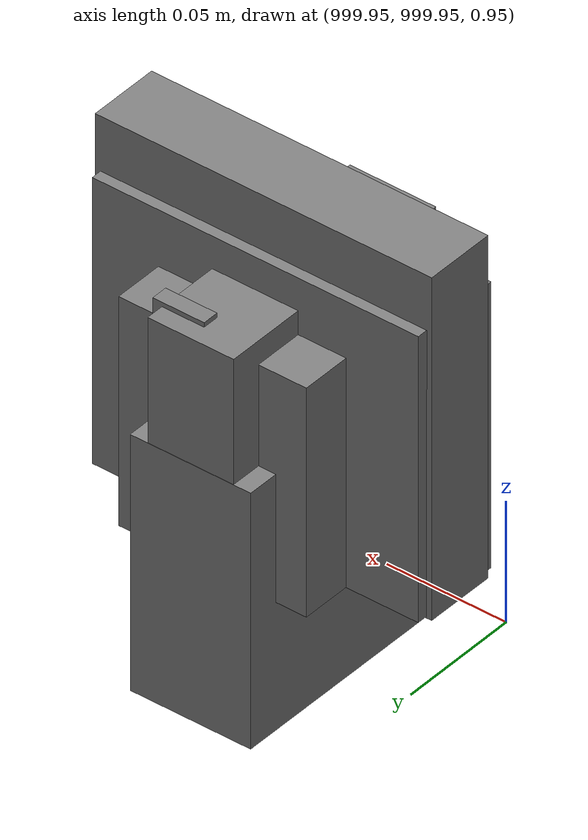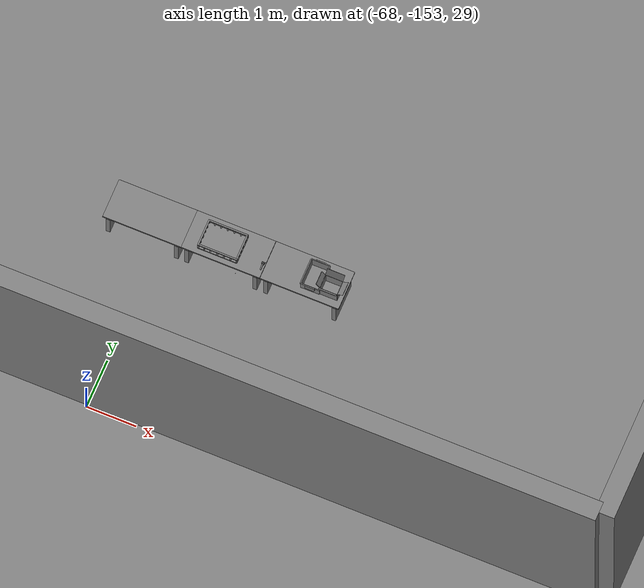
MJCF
<mujoco>
    <option gravity="0.000000000 0.000000000 -9.810000420" timestep="0.0049999999" integrator="implicitfast" density="1.225" viscosity="1.8000001e-05" noslip_iterations="10" iterations="100" sdf_iterations="50">
        <flag multiccd="disable"/>
    </option>
    <size memory="1000M"/>
    <compiler coordinate="local"/>
    <worldbody>
        <light cutoff="30" pos="0 1 1" dir="0 -1 -2"/>
        <light cutoff="30" pos="0 -1 1" dir="0 1 -2"/>
        <body pos="-64.866622925 -149.383972168 30.183746338" euler="89.999984741 89.999946594 0.000000000" name="openloong_gripper_2f85_fix_base_usda_bluebox_01">
            <geom contype="1" conaffinity="1" density="1000" type="box" material="" rgba="0.500000000 0.500000000 0.500000000 1.000000000" solimp="0.899999976 0.949999988 0.001000000" friction="1.000000000 0.005000000 0.000100000" solref="0.020000000 1.000000000" margin="0" condim="3" group="0" pos="0.276580811 0.187225342 0.000068665" quat="0.707106948 0.000077471 0.707106352 0.000077486" size="0.100000001 0.057999998 0.010000000" name="openloong_gripper_2f85_fix_base_usda_geom_11218F7A_E017_4992_8248_37A7B3DF9385"/>
            <geom contype="1" conaffinity="1" density="1000" type="box" material="" rgba="0.500000000 0.500000000 0.500000000 1.000000000" solimp="0.899999976 0.949999988 0.001000000" friction="1.000000000 0.005000000 0.000100000" solref="0.020000000 1.000000000" margin="0" condim="3" group="0" pos="0.000000000 0.002883911 0.000000000" quat="0.999999881 0.000000000 0.000000000 0.000000000" size="0.254000008 0.003000000 0.172000006" name="openloong_gripper_2f85_fix_base_usda_geom_EE3D23CA_24E5_4FA6_A72B_819769D1BA19"/>
            <geom contype="1" conaffinity="1" density="1000" type="box" material="" rgba="0.500000000 0.500000000 0.500000000 1.000000000" solimp="0.899999976 0.949999988 0.001000000" friction="1.000000000 0.005000000 0.000100000" solref="0.020000000 1.000000000" margin="0" condim="3" group="0" pos="0.000000000 0.124874115 0.173484802" quat="0.999796331 0.020176515 -0.000000015 0.000000030" size="0.259999990 0.119999997 0.007000000" name="openloong_gripper_2f85_fix_base_usda_geom_CAB889E4_B7F3_43C4_A011_921A0A51DE8D"/>
            <geom contype="1" conaffinity="1" density="1000" type="box" material="" rgba="0.500000000 0.500000000 0.500000000 1.000000000" solimp="0.899999976 0.949999988 0.001000000" friction="1.000000000 0.005000000 0.000100000" solref="0.020000000 1.000000000" margin="0" condim="3" group="0" pos="0.000000000 0.124874115 -0.173469543" quat="0.999796331 -0.020176545 -0.000000015 0.000000000" size="0.259999990 0.119999997 0.007000000" name="openloong_gripper_2f85_fix_base_usda_geom_DF7770FC_A3F0_4FCD_B0B0_D96D4C367E95"/>
            <geom contype="1" conaffinity="1" density="1000" type="box" material="" rgba="0.500000000 0.500000000 0.500000000 1.000000000" solimp="0.899999976 0.949999988 0.001000000" friction="1.000000000 0.005000000 0.000100000" solref="0.020000000 1.000000000" margin="0" condim="3" group="0" pos="0.000000000 0.214008331 0.188980103" quat="0.999912977 0.013176724 0.000000015 0.000000000" size="0.259999990 0.029999999 0.012500000" name="openloong_gripper_2f85_fix_base_usda_geom_5D52C6C6_7422_4D05_86C7_A30CD048877A"/>
            <geom contype="1" conaffinity="1" density="1000" type="box" material="" rgba="0.500000000 0.500000000 0.500000000 1.000000000" solimp="0.899999976 0.949999988 0.001000000" friction="1.000000000 0.005000000 0.000100000" solref="0.020000000 1.000000000" margin="0" condim="3" group="0" pos="-0.258361816 0.125289917 0.001876831" quat="0.702796936 -0.020792112 0.710783124 0.020769298" size="0.189999998 0.119999997 0.009000000" name="openloong_gripper_2f85_fix_base_usda_geom_468DD66D_99FD_4AB1_A909_2B1675CFE231"/>
            <geom contype="1" conaffinity="1" density="1000" type="box" material="" rgba="0.500000000 0.500000000 0.500000000 1.000000000" solimp="0.899999976 0.949999988 0.001000000" friction="1.000000000 0.005000000 0.000100000" solref="0.020000000 1.000000000" margin="0" condim="3" group="0" pos="0.000000000 0.214008331 -0.188980103" quat="0.999912977 -0.013176769 0.000000030 0.000000015" size="0.259999990 0.029999999 0.012500000" name="openloong_gripper_2f85_fix_base_usda_geom_41549C92_9903_4FDA_9E1A_BEB05303982D"/>
            <geom contype="1" conaffinity="1" density="1000" type="box" material="" rgba="0.500000000 0.500000000 0.500000000 1.000000000" solimp="0.899999976 0.949999988 0.001000000" friction="1.000000000 0.005000000 0.000100000" solref="0.020000000 1.000000000" margin="0" condim="3" group="0" pos="-0.276611328 0.187225342 0.000068665" quat="0.707106650 0.000077441 0.707106709 0.000077456" size="0.100000001 0.057999998 0.010000000" name="openloong_gripper_2f85_fix_base_usda_geom_7C847992_4CA3_48D6_9533_B9D66142C207"/>
            <geom contype="1" conaffinity="1" density="1000" type="box" material="" rgba="0.500000000 0.500000000 0.500000000 1.000000000" solimp="0.899999976 0.949999988 0.001000000" friction="1.000000000 0.005000000 0.000100000" solref="0.020000000 1.000000000" margin="0" condim="3" group="0" pos="0.258331299 0.125289917 0.001876831" quat="0.702851415 0.018856421 0.710823774 -0.019329369" size="0.189999998 0.119999997 0.009000000" name="openloong_gripper_2f85_fix_base_usda_geom_E8A54ED0_AF82_44D9_B3BA_A6760EDC6B64"/>
            <freejoint name="openloong_gripper_2f85_fix_base_usda_bluebox_01_joint"/>
            <site size="0.005000000 0.005000000 0.005000000" rgba="0.500000000 0.500000000 0.500000000 1.000000000" pos="0.000000000 0.000000000 0.000000000" quat="0.999961913 0.008726534 0.000000000 0.000000000" group="0" type="sphere" name="openloong_gripper_2f85_fix_base_usda_bluebox_01site"/>
        </body>
        <body pos="-64.496299744 -149.491867065 30.235729218" euler="0.000000000 0.000000000 89.999946594" name="openloong_gripper_2f85_fix_base_usda_cardboardbox_01">
            <geom contype="1" conaffinity="1" density="1000" type="box" material="" rgba="0.500000000 0.500000000 0.500000000 1.000000000" solimp="0.899999976 0.949999988 0.001000000" friction="1.000000000 0.005000000 0.000100000" solref="0.020000000 1.000000000" margin="0" condim="3" group="0" pos="-0.003166199 -0.004086494 0.005052090" quat="1.000000000 0.000000000 0.000000000 0.000000000" size="0.142499998 0.177500010 0.005000000" name="openloong_gripper_2f85_fix_base_usda_geom_6CF5C457_0273_4165_9A52_13CEDE411A41"/>
            <geom contype="1" conaffinity="1" density="1000" type="box" material="" rgba="0.500000000 0.500000000 0.500000000 1.000000000" solimp="0.899999976 0.949999988 0.001000000" friction="1.000000000 0.005000000 0.000100000" solref="0.020000000 1.000000000" margin="0" condim="3" group="0" pos="-0.003166199 0.170316696 0.150570869" quat="1.000000000 0.000000000 0.000000000 0.000000000" size="0.142499998 0.005000000 0.149999991" name="openloong_gripper_2f85_fix_base_usda_geom_052C4767_C253_4EAA_85DF_9CFFB6568B1B"/>
            <geom contype="1" conaffinity="1" density="1000" type="box" material="" rgba="0.500000000 0.500000000 0.500000000 1.000000000" solimp="0.899999976 0.949999988 0.001000000" friction="1.000000000 0.005000000 0.000100000" solref="0.020000000 1.000000000" margin="0" condim="3" group="0" pos="-0.147399902 -0.005307198 0.150570869" quat="1.000000000 0.000000000 0.000000000 0.000000000" size="0.005000000 0.177500010 0.149999991" name="openloong_gripper_2f85_fix_base_usda_geom_05CC52EB_821C_460F_AAA8_4A35AA46A904"/>
            <geom contype="1" conaffinity="1" density="1000" type="box" material="" rgba="0.500000000 0.500000000 0.500000000 1.000000000" solimp="0.899999976 0.949999988 0.001000000" friction="1.000000000 0.005000000 0.000100000" solref="0.020000000 1.000000000" margin="0" condim="3" group="0" pos="0.140275955 -0.005307198 0.150570869" quat="1.000000000 0.000000000 0.000000000 0.000000000" size="0.005000000 0.177500010 0.149999991" name="openloong_gripper_2f85_fix_base_usda_geom_09ECD230_5935_4A29_A7EB_F425C5CF0539"/>
            <geom contype="1" conaffinity="1" density="1000" type="box" material="" rgba="0.500000000 0.500000000 0.500000000 1.000000000" solimp="0.899999976 0.949999988 0.001000000" friction="1.000000000 0.005000000 0.000100000" solref="0.020000000 1.000000000" margin="0" condim="3" group="0" pos="-0.003166199 -0.181550980 0.150570869" quat="1.000000000 0.000000000 0.000000000 0.000000000" size="0.142499998 0.005000000 0.149999991" name="openloong_gripper_2f85_fix_base_usda_geom_2F51E577_8E07_4F0F_B10E_C2AC4C4656C3"/>
            <freejoint name="openloong_gripper_2f85_fix_base_usda_cardboardbox_01_joint"/>
            <site size="0.005000000 0.005000000 0.005000000" rgba="0.500000000 0.500000000 0.500000000 1.000000000" pos="0.000000000 0.000000000 0.000000000" quat="0.999961913 0.008726535 0.000000000 0.000000000" group="0" type="sphere" name="openloong_gripper_2f85_fix_base_usda_site_AF19BF0B_4FDE_4DA6_A858_EAE65B2927D2"/>
            <body pos="0.139160156 -0.004048347 0.301930904" euler="-179.999954224 49.383502960 179.999954224" name="openloong_gripper_2f85_fix_base_usda_A1_006">
                <geom contype="1" conaffinity="1" density="1000" type="box" material="" rgba="0.500000000 0.500000000 0.500000000 1.000000000" solimp="0.899999976 0.949999988 0.001000000" friction="1.000000000 0.005000000 0.000100000" solref="0.020000000 1.000000000" margin="0" condim="3" group="0" pos="-0.071587563 0.000009537 0.001745224" quat="0.999999881 0.000000000 0.000000000 0.000000000" size="0.071249999 0.179999992 0.002500000" name="openloong_gripper_2f85_fix_base_usda_geom_0C22D951_0725_49FD_BB56_5A8F57C3B096"/>
                <joint armature="0" stiffness="0.07" damping="0.0099999998" axis="0.000000 1.000000 0.000000" type="hinge" name="openloong_gripper_2f85_fix_base_usda_A1_006"/>
            </body>
            <body pos="-0.145902634 -0.004086494 0.301938057" euler="-180.000000000 -60.000011444 -180.000000000" name="openloong_gripper_2f85_fix_base_usda_A2_006">
                <geom contype="1" conaffinity="1" density="1000" type="box" material="" rgba="0.500000000 0.500000000 0.500000000 1.000000000" solimp="0.899999976 0.949999988 0.001000000" friction="1.000000000 0.005000000 0.000100000" solref="0.020000000 1.000000000" margin="0" condim="3" group="0" pos="0.071268082 0.000009537 0.002717972" quat="0.000002921 0.000000000 -0.000000030 0.999999881" size="0.071249999 0.179999992 0.002500000" name="openloong_gripper_2f85_fix_base_usda_geom_69AF2A89_94B7_42ED_9AB2_57067A854C01"/>
                <joint armature="0" stiffness="0.07" damping="0.0099999998" axis="0.000000 1.000000 0.000000" type="hinge" name="openloong_gripper_2f85_fix_base_usda_A2_006"/>
            </body>
            <body pos="-0.003385544 0.175991058 0.301930904" euler="-125.858116150 -0.000004561 0.000002331" name="openloong_gripper_2f85_fix_base_usda_B2_006">
                <geom contype="1" conaffinity="1" density="1000" type="box" material="" rgba="0.500000000 0.500000000 0.500000000 1.000000000" solimp="0.899999976 0.949999988 0.001000000" friction="1.000000000 0.005000000 0.000100000" solref="0.020000000 1.000000000" margin="0" condim="3" group="0" pos="0.000009537 -0.070939064 -0.002470016" quat="0.999614120 0.027776197 -0.000000015 0.000000030" size="0.137500003 0.064999998 0.005000000" name="openloong_gripper_2f85_fix_base_usda_geom_A08E1279_493A_418D_B23A_ECF3B3B5F7ED"/>
                <joint armature="0" stiffness="0.07" damping="0.0099999998" axis="1.000000 0.000000 0.000000" type="hinge" name="openloong_gripper_2f85_fix_base_usda_B2_006"/>
            </body>
            <body pos="-0.003385544 -0.184140205 0.301938057" euler="147.805557251 0.000000000 0.000000000" name="openloong_gripper_2f85_fix_base_usda_B1_006">
                <geom contype="1" conaffinity="1" density="1000" type="box" material="" rgba="0.500000000 0.500000000 0.500000000 1.000000000" solimp="0.899999976 0.949999988 0.001000000" friction="1.000000000 0.005000000 0.000100000" solref="0.020000000 1.000000000" margin="0" condim="3" group="0" pos="-0.000028610 0.070202351 -0.002703667" quat="0.999614179 -0.027776167 0.000000000 0.000000000" size="0.137500003 0.064999998 0.005000000" name="openloong_gripper_2f85_fix_base_usda_geom_C01394E4_92C4_4A08_BD56_01C62DEB687D"/>
                <joint armature="0" stiffness="0.07" damping="0.0099999998" axis="1.000000 0.000000 0.000000" type="hinge" name="openloong_gripper_2f85_fix_base_usda_B1_006"/>
            </body>
        </body>
        <body pos="-65.882858276 -149.481979370 30.229999542" euler="-64.487716675 0.000000000 0.000000000" name="openloong_gripper_2f85_fix_base_usda_Barcode">
            <geom contype="1" conaffinity="1" density="1000" type="box" material="" rgba="0.500000000 0.500000000 0.500000000 1.000000000" solimp="0.899999976 0.949999988 0.001000000" friction="1.000000000 0.005000000 0.000100000" solref="0.020000000 1.000000000" margin="0" condim="3" group="0" pos="0.000000000 0.013038635 0.001419067" quat="0.000000000 0.000000000 0.000000000 1.000000119" size="0.034000002 0.010000000 0.017999999" name="openloong_gripper_2f85_fix_base_usda_geom_672A511C_9241_409B_8698_B1ACD80BAF08"/>
            <geom contype="1" conaffinity="1" density="1000" type="box" material="" rgba="0.500000000 0.500000000 0.500000000 1.000000000" solimp="0.899999976 0.949999988 0.001000000" friction="1.000000000 0.005000000 0.000100000" solref="0.020000000 1.000000000" margin="0" condim="3" group="0" pos="0.000000000 -0.035301208 -0.007095337" quat="0.000000000 0.000000000 -0.043619365 0.999048233" size="0.028999999 0.010000000 0.020000000" name="openloong_gripper_2f85_fix_base_usda_geom_B7306200_8A5D_480C_8EF0_3694BE0C51F8"/>
            <geom contype="1" conaffinity="1" density="1000" type="box" material="" rgba="0.500000000 0.500000000 0.500000000 1.000000000" solimp="0.899999976 0.949999988 0.001000000" friction="1.000000000 0.005000000 0.000100000" solref="0.020000000 1.000000000" margin="0" condim="3" group="0" pos="0.000000000 -0.043411255 -0.011749268" quat="0.922262907 0.386563420 0.000000000 0.000000000" size="0.026000001 0.010000000 0.020000000" name="openloong_gripper_2f85_fix_base_usda_geom_868B4AB3_79CF_418E_96A6_2401B8B77CC7"/>
            <geom contype="1" conaffinity="1" density="1000" type="box" material="" rgba="0.500000000 0.500000000 0.500000000 1.000000000" solimp="0.899999976 0.949999988 0.001000000" friction="1.000000000 0.005000000 0.000100000" solref="0.020000000 1.000000000" margin="0" condim="3" group="0" pos="0.000000000 -0.016967773 -0.031860352" quat="0.000000000 0.000000000 0.000000000 1.000000119" size="0.008000000 0.010000000 0.013000000" name="openloong_gripper_2f85_fix_base_usda_geom_9C92E9DB_E422_4AE2_8361_7B8700502CB9"/>
            <geom contype="1" conaffinity="1" density="1000" type="box" material="" rgba="0.500000000 0.500000000 0.500000000 1.000000000" solimp="0.899999976 0.949999988 0.001000000" friction="1.000000000 0.005000000 0.000100000" solref="0.020000000 1.000000000" margin="0" condim="3" group="0" pos="0.000000000 -0.001869202 0.000312805" quat="0.953716993 0.300705761 0.000000000 0.000000000" size="0.032000002 0.010000000 0.018999999" name="openloong_gripper_2f85_fix_base_usda_geom_7A153169_0A4C_42EE_8586_D2589F4A4304"/>
            <geom contype="1" conaffinity="1" density="1000" type="box" material="" rgba="0.500000000 0.500000000 0.500000000 1.000000000" solimp="0.899999976 0.949999988 0.001000000" friction="1.000000000 0.005000000 0.000100000" solref="0.020000000 1.000000000" margin="0" condim="3" group="0" pos="0.000000000 -0.019531250 -0.003173828" quat="0.953716993 0.300705761 0.000000000 0.000000000" size="0.030999999 0.010000000 0.020000000" name="openloong_gripper_2f85_fix_base_usda_geom_BA5EB3E0_8B80_4D6C_81D2_FE8440D8F67A"/>
            <geom contype="1" conaffinity="1" density="1000" type="box" material="" rgba="0.500000000 0.500000000 0.500000000 1.000000000" solimp="0.899999976 0.949999988 0.001000000" friction="1.000000000 0.005000000 0.000100000" solref="0.020000000 1.000000000" margin="0" condim="3" group="0" pos="0.000000000 -0.035301208 -0.007095337" quat="0.953716993 0.300705761 0.000000000 0.000000000" size="0.028999999 0.010000000 0.020000000" name="openloong_gripper_2f85_fix_base_usda_geom_8359D156_32CB_438C_93D9_9A4B77319CF8"/>
            <geom contype="1" conaffinity="1" density="1000" type="box" material="" rgba="0.500000000 0.500000000 0.500000000 1.000000000" solimp="0.899999976 0.949999988 0.001000000" friction="1.000000000 0.005000000 0.000100000" solref="0.020000000 1.000000000" margin="0" condim="3" group="0" pos="0.000000000 -0.042617798 -0.071121216" quat="0.000000000 0.000000000 0.000000000 1.000000119" size="0.013000000 0.021000000 0.059999999" name="openloong_gripper_2f85_fix_base_usda_geom_AD63DAF8_B64A_4FDD_9815_C831D38E5A21"/>
            <freejoint name="openloong_gripper_2f85_fix_base_usda_Barcode_joint"/>
            <site size="0.005000000 0.005000000 0.005000000" rgba="0.500000000 0.500000000 0.500000000 1.000000000" pos="0.000000000 0.000000000 0.000000000" quat="1.000000000 0.000000000 0.000000000 0.000000000" group="0" type="sphere" name="openloong_gripper_2f85_fix_base_usda_Barcode_site"/>
        </body>
        <body pos="-66.745018005 -149.392349243 30.184000015" euler="0.000000000 0.000000000 89.999946594" name="[22333396428231]_Basket_01">
            <geom contype="1" conaffinity="1" density="1000" type="box" material="" rgba="0.500000000 0.500000000 0.500000000 1.000000000" solimp="0.899999976 0.949999988 0.001000000" friction="1.000000000 0.005000000 0.000100000" solref="0.020000000 1.000000000" margin="0" condim="3" group="0" pos="-0.052425385 0.389207840 0.089787483" quat="0.707107008 0.000000000 0.000000000 0.707106411" size="0.014249999 0.014249999 0.059999999" name="[22333396428231]_geom_1CD0C202_BEF7_461C_B79F_EFE2C4315091"/>
            <geom contype="1" conaffinity="1" density="1000" type="box" material="" rgba="0.500000000 0.500000000 0.500000000 1.000000000" solimp="0.899999976 0.949999988 0.001000000" friction="1.000000000 0.005000000 0.000100000" solref="0.020000000 1.000000000" margin="0" condim="3" group="0" pos="0.264015198 -0.133043289 0.089787483" quat="0.707107008 0.000000000 0.000000000 0.707106411" size="0.014249999 0.014249999 0.059999999" name="[22333396428231]_geom_A2447B06_0653_4BCD_8777_5FE0CDCA3F4C"/>
            <geom contype="1" conaffinity="1" density="1000" type="box" material="" rgba="0.500000000 0.500000000 0.500000000 1.000000000" solimp="0.899999976 0.949999988 0.001000000" friction="1.000000000 0.005000000 0.000100000" solref="0.020000000 1.000000000" margin="0" condim="3" group="0" pos="-0.264015198 -0.265548706 0.089793205" quat="0.707107008 0.000000000 0.000000000 0.707106411" size="0.014249999 0.014249999 0.059999999" name="[22333396428231]_geom_99E983A2_3CC3_4BA8_BB58_2D6EE0510760"/>
            <geom contype="1" conaffinity="1" density="1000" type="box" material="" rgba="0.500000000 0.500000000 0.500000000 1.000000000" solimp="0.899999976 0.949999988 0.001000000" friction="1.000000000 0.005000000 0.000100000" solref="0.020000000 1.000000000" margin="0" condim="3" group="0" pos="-0.160263062 -0.389322281 0.089793205" quat="0.707107008 0.000000000 0.000000000 0.707106411" size="0.014249999 0.014249999 0.059999999" name="[22333396428231]_geom_1AC85C26_71FC_4548_9077_17AA923D7532"/>
            <geom contype="1" conaffinity="1" density="1000" type="box" material="" rgba="0.500000000 0.500000000 0.500000000 1.000000000" solimp="0.899999976 0.949999988 0.001000000" friction="1.000000000 0.005000000 0.000100000" solref="0.020000000 1.000000000" margin="0" condim="3" group="0" pos="0.162265778 -0.389322281 0.089787483" quat="0.707107008 0.000000000 0.000000000 0.707106411" size="0.014249999 0.014249999 0.059999999" name="[22333396428231]_geom_74DD83C5_E747_42B0_9F9A_C5DA0F861238"/>
            <geom contype="1" conaffinity="1" density="1000" type="box" material="" rgba="0.500000000 0.500000000 0.500000000 1.000000000" solimp="0.899999976 0.949999988 0.001000000" friction="1.000000000 0.005000000 0.000100000" solref="0.020000000 1.000000000" margin="0" condim="3" group="0" pos="0.264015198 0.389207840 0.089787483" quat="0.707107008 0.000000000 0.000000000 0.707106411" size="0.014249999 0.014249999 0.059999999" name="[22333396428231]_geom_47B15076_5440_45C7_B811_606C3D1061A9"/>
            <geom contype="1" conaffinity="1" density="1000" type="box" material="" rgba="0.500000000 0.500000000 0.500000000 1.000000000" solimp="0.899999976 0.949999988 0.001000000" friction="1.000000000 0.005000000 0.000100000" solref="0.020000000 1.000000000" margin="0" condim="3" group="0" pos="-0.264015198 -0.133043289 0.089793205" quat="0.707107008 0.000000000 0.000000000 0.707106411" size="0.014249999 0.014249999 0.059999999" name="[22333396428231]_geom_D663EA09_1C9A_47F3_B9F5_C4A878BF4DF8"/>
            <geom contype="1" conaffinity="1" density="1000" type="box" material="" rgba="0.500000000 0.500000000 0.500000000 1.000000000" solimp="0.899999976 0.949999988 0.001000000" friction="1.000000000 0.005000000 0.000100000" solref="0.020000000 1.000000000" margin="0" condim="3" group="0" pos="-0.264026642 0.269256592 0.089793205" quat="0.707107008 0.000000000 0.000000000 0.707106411" size="0.014249999 0.014249999 0.059999999" name="[22333396428231]_geom_DFB784F0_7B87_47C3_99F3_D288519566CD"/>
            <geom contype="1" conaffinity="1" density="1000" type="box" material="" rgba="0.500000000 0.500000000 0.500000000 1.000000000" solimp="0.899999976 0.949999988 0.001000000" friction="1.000000000 0.005000000 0.000100000" solref="0.020000000 1.000000000" margin="0" condim="3" group="0" pos="0.054462433 0.389207840 0.089787483" quat="0.707107008 0.000000000 0.000000000 0.707106411" size="0.014249999 0.014249999 0.059999999" name="[22333396428231]_geom_A4B2B943_9B99_4974_B27F_DAD13B3E34DD"/>
            <geom contype="1" conaffinity="1" density="1000" type="box" material="" rgba="0.500000000 0.500000000 0.500000000 1.000000000" solimp="0.899999976 0.949999988 0.001000000" friction="1.000000000 0.005000000 0.000100000" solref="0.020000000 1.000000000" margin="0" condim="3" group="0" pos="0.054462433 -0.389322281 0.089787483" quat="0.707107008 0.000000000 0.000000000 0.707106411" size="0.014249999 0.014249999 0.059999999" name="[22333396428231]_geom_0F8E5485_48F9_41E8_AA05_A2D50649AFAF"/>
            <geom contype="1" conaffinity="1" density="1000" type="box" material="" rgba="0.500000000 0.500000000 0.500000000 1.000000000" solimp="0.899999976 0.949999988 0.001000000" friction="1.000000000 0.005000000 0.000100000" solref="0.020000000 1.000000000" margin="0" condim="3" group="0" pos="0.264015198 0.269256592 0.089793205" quat="0.707107008 0.000000000 0.000000000 0.707106411" size="0.014249999 0.014249999 0.059999999" name="[22333396428231]_geom_D5837AFB_52A8_42A5_83B7_74C11E6CCD4F"/>
            <geom contype="1" conaffinity="1" density="1000" type="box" material="" rgba="0.500000000 0.500000000 0.500000000 1.000000000" solimp="0.899999976 0.949999988 0.001000000" friction="1.000000000 0.005000000 0.000100000" solref="0.020000000 1.000000000" margin="0" condim="3" group="0" pos="0.264015198 -0.389322281 0.089787483" quat="0.707107008 0.000000000 0.000000000 0.707106411" size="0.014249999 0.014249999 0.059999999" name="[22333396428231]_geom_B2AFD32B_8493_4956_B332_39525DB1F091"/>
            <geom contype="1" conaffinity="1" density="1000" type="box" material="" rgba="0.500000000 0.500000000 0.500000000 1.000000000" solimp="0.899999976 0.949999988 0.001000000" friction="1.000000000 0.005000000 0.000100000" solref="0.020000000 1.000000000" margin="0" condim="3" group="0" pos="0.000000000 0.000000000 0.015998840" quat="0.707107008 0.000000000 0.000000000 0.707106411" size="0.403499991 0.279000014 0.015750000" name="[22333396428231]_geom_B4824D98_BB39_4B2C_8D99_E2EC86B39A8B"/>
            <geom contype="1" conaffinity="1" density="1000" type="box" material="" rgba="0.500000000 0.500000000 0.500000000 1.000000000" solimp="0.899999976 0.949999988 0.001000000" friction="1.000000000 0.005000000 0.000100000" solref="0.020000000 1.000000000" margin="0" condim="3" group="0" pos="0.000000000 -0.389476776 0.163619041" quat="0.707107008 0.000000000 0.000000000 0.707106411" size="0.015000000 0.277500004 0.015750000" name="[22333396428231]_geom_77E81D00_9F92_437D_B11C_64F3974C10AB"/>
            <geom contype="1" conaffinity="1" density="1000" type="box" material="" rgba="0.500000000 0.500000000 0.500000000 1.000000000" solimp="0.899999976 0.949999988 0.001000000" friction="1.000000000 0.005000000 0.000100000" solref="0.020000000 1.000000000" margin="0" condim="3" group="0" pos="0.162265778 0.389207840 0.089787483" quat="0.707107008 0.000000000 0.000000000 0.707106411" size="0.014249999 0.014249999 0.059999999" name="[22333396428231]_geom_92E7366D_E373_4EFA_8391_F459473E90FF"/>
            <geom contype="1" conaffinity="1" density="1000" type="box" material="" rgba="0.500000000 0.500000000 0.500000000 1.000000000" solimp="0.899999976 0.949999988 0.001000000" friction="1.000000000 0.005000000 0.000100000" solref="0.020000000 1.000000000" margin="0" condim="3" group="0" pos="0.000000000 0.389471054 0.163619041" quat="0.707107008 0.000000000 0.000000000 0.707106411" size="0.015000000 0.277500004 0.015750000" name="[22333396428231]_geom_BE185844_FA42_43B2_B162_39076761C7A1"/>
            <geom contype="1" conaffinity="1" density="1000" type="box" material="" rgba="0.500000000 0.500000000 0.500000000 1.000000000" solimp="0.899999976 0.949999988 0.001000000" friction="1.000000000 0.005000000 0.000100000" solref="0.020000000 1.000000000" margin="0" condim="3" group="0" pos="-0.263511658 0.000000000 0.163619041" quat="0.707107008 0.000000000 0.000000000 0.707106411" size="0.403499991 0.015000000 0.015750000" name="[22333396428231]_geom_4969CA2C_EFF2_45D8_995F_9DC5C53520CF"/>
            <geom contype="1" conaffinity="1" density="1000" type="box" material="" rgba="0.500000000 0.500000000 0.500000000 1.000000000" solimp="0.899999976 0.949999988 0.001000000" friction="1.000000000 0.005000000 0.000100000" solref="0.020000000 1.000000000" margin="0" condim="3" group="0" pos="-0.264015198 0.141334534 0.089793205" quat="0.707107008 0.000000000 0.000000000 0.707106411" size="0.014249999 0.014249999 0.059999999" name="[22333396428231]_geom_620ACECD_112C_4AD9_A8B7_CC413A44567E"/>
            <geom contype="1" conaffinity="1" density="1000" type="box" material="" rgba="0.500000000 0.500000000 0.500000000 1.000000000" solimp="0.899999976 0.949999988 0.001000000" friction="1.000000000 0.005000000 0.000100000" solref="0.020000000 1.000000000" margin="0" condim="3" group="0" pos="0.264015198 -0.265548706 0.089787483" quat="0.707107008 0.000000000 0.000000000 0.707106411" size="0.014249999 0.014249999 0.059999999" name="[22333396428231]_geom_0E4A3B53_8A0E_4E96_A957_6ABB40761F83"/>
            <geom contype="1" conaffinity="1" density="1000" type="box" material="" rgba="0.500000000 0.500000000 0.500000000 1.000000000" solimp="0.899999976 0.949999988 0.001000000" friction="1.000000000 0.005000000 0.000100000" solref="0.020000000 1.000000000" margin="0" condim="3" group="0" pos="-0.160263062 0.389207840 0.089787483" quat="0.707107008 0.000000000 0.000000000 0.707106411" size="0.014249999 0.014249999 0.059999999" name="[22333396428231]_geom_F3C749FD_17CD_409F_880D_CEBFB59095B7"/>
            <geom contype="1" conaffinity="1" density="1000" type="box" material="" rgba="0.500000000 0.500000000 0.500000000 1.000000000" solimp="0.899999976 0.949999988 0.001000000" friction="1.000000000 0.005000000 0.000100000" solref="0.020000000 1.000000000" margin="0" condim="3" group="0" pos="-0.052425385 -0.389322281 0.089787483" quat="0.707107008 0.000000000 0.000000000 0.707106411" size="0.014249999 0.014249999 0.059999999" name="[22333396428231]_geom_1512129B_3035_46C6_9159_5250A3F1E7EE"/>
            <geom contype="1" conaffinity="1" density="1000" type="box" material="" rgba="0.500000000 0.500000000 0.500000000 1.000000000" solimp="0.899999976 0.949999988 0.001000000" friction="1.000000000 0.005000000 0.000100000" solref="0.020000000 1.000000000" margin="0" condim="3" group="0" pos="-0.264026642 -0.389322281 0.089793205" quat="0.707107008 0.000000000 0.000000000 0.707106411" size="0.014249999 0.014249999 0.059999999" name="[22333396428231]_geom_8CF8D80C_89AE_475A_8D6E_CE0B5A249355"/>
            <geom contype="1" conaffinity="1" density="1000" type="box" material="" rgba="0.500000000 0.500000000 0.500000000 1.000000000" solimp="0.899999976 0.949999988 0.001000000" friction="1.000000000 0.005000000 0.000100000" solref="0.020000000 1.000000000" margin="0" condim="3" group="0" pos="0.264015198 0.141334534 0.089787483" quat="0.707107008 0.000000000 0.000000000 0.707106411" size="0.014249999 0.014249999 0.059999999" name="[22333396428231]_geom_2DA98DAC_6EC4_4DD1_B1FE_F05F1DD82271"/>
            <geom contype="1" conaffinity="1" density="1000" type="box" material="" rgba="0.500000000 0.500000000 0.500000000 1.000000000" solimp="0.899999976 0.949999988 0.001000000" friction="1.000000000 0.005000000 0.000100000" solref="0.020000000 1.000000000" margin="0" condim="3" group="0" pos="-0.264015198 0.389207840 0.089793205" quat="0.707107008 0.000000000 0.000000000 0.707106411" size="0.014249999 0.014249999 0.059999999" name="[22333396428231]_geom_A216430A_9A9C_4BF0_A168_84949FA28876"/>
            <geom contype="1" conaffinity="1" density="1000" type="box" material="" rgba="0.500000000 0.500000000 0.500000000 1.000000000" solimp="0.899999976 0.949999988 0.001000000" friction="1.000000000 0.005000000 0.000100000" solref="0.020000000 1.000000000" margin="0" condim="3" group="0" pos="0.264015198 0.004480362 0.089787483" quat="0.707107008 0.000000000 0.000000000 0.707106411" size="0.014249999 0.014249999 0.059999999" name="[22333396428231]_geom_3BFFC1BC_066F_430D_BBE0_AB47C61DFCC2"/>
            <geom contype="1" conaffinity="1" density="1000" type="box" material="" rgba="0.500000000 0.500000000 0.500000000 1.000000000" solimp="0.899999976 0.949999988 0.001000000" friction="1.000000000 0.005000000 0.000100000" solref="0.020000000 1.000000000" margin="0" condim="3" group="0" pos="0.263694763 -0.000011444 0.163619041" quat="0.707107008 0.000000000 0.000000000 0.707106411" size="0.403499991 0.015000000 0.015750000" name="[22333396428231]_geom_12E0156D_089C_492A_81D7_B61F8532C144"/>
            <geom contype="1" conaffinity="1" density="1000" type="box" material="" rgba="0.500000000 0.500000000 0.500000000 1.000000000" solimp="0.899999976 0.949999988 0.001000000" friction="1.000000000 0.005000000 0.000100000" solref="0.020000000 1.000000000" margin="0" condim="3" group="0" pos="-0.264015198 0.004480362 0.089793205" quat="0.707107008 0.000000000 0.000000000 0.707106411" size="0.014249999 0.014249999 0.059999999" name="[22333396428231]_geom_10C73792_AA4B_433D_9654_43473464E34D"/>
            <freejoint name="[22333396428231]_joint_2719C24E_DAEC_42B7_B43B_5DE71B9DB82C"/>
        </body>
        <body pos="0.000000000 0.000000000 0.000000000" euler="0.000000000 0.000000000 0.000000000" name="Static Objects_Static Objects">
            <geom contype="1" conaffinity="1" density="1000" type="box" material="" rgba="0.500000000 0.500000000 0.500000000 1.000000000" solimp="0.899999976 0.949999988 0.001000000" friction="1.000000000 0.005000000 0.000100000" solref="0.020000000 1.000000000" margin="0" condim="3" group="0" pos="-67.544113159 -149.365814209 29.727830887" quat="0.500000417 0.499999970 0.499999553 0.499999970" size="0.381000012 0.319999993 0.041000001" name="Static Objects_geom_5128BF43_6D8B_49AE_BA6D_28DB435955EE"/>
            <geom contype="1" conaffinity="1" density="1000" type="box" material="" rgba="0.500000000 0.500000000 0.500000000 1.000000000" solimp="0.899999976 0.949999988 0.001000000" friction="1.000000000 0.005000000 0.000100000" solref="0.020000000 1.000000000" margin="0" condim="3" group="0" pos="-68.239501953 -149.365814209 30.086868286" quat="0.500000417 0.499999970 0.499999553 0.499999970" size="0.370999992 0.039500002 0.745000005" name="Static Objects_geom_E43CA86E_0A62_48B7_98FD_A405DC201816"/>
            <geom contype="1" conaffinity="1" density="1000" type="box" material="" rgba="0.500000000 0.500000000 0.500000000 1.000000000" solimp="0.899999976 0.949999988 0.001000000" friction="1.000000000 0.005000000 0.000100000" solref="0.020000000 1.000000000" margin="0" condim="3" group="0" pos="-68.239501953 -149.365814209 30.147235870" quat="0.500000417 0.499999970 0.499999553 0.499999970" size="0.400000006 0.022000000 0.800000012" name="Static Objects_geom_0FB851E4_9D35_47D5_93A2_66B1BD79304C"/>
            <geom contype="1" conaffinity="1" density="1000" type="box" material="" rgba="0.500000000 0.500000000 0.500000000 1.000000000" solimp="0.899999976 0.949999988 0.001000000" friction="1.000000000 0.005000000 0.000100000" solref="0.020000000 1.000000000" margin="0" condim="3" group="0" pos="-68.934890747 -149.365814209 29.727830887" quat="0.500000417 0.499999970 0.499999553 0.499999970" size="0.381000012 0.319999993 0.041000001" name="Static Objects_geom_EEBD3DE1_8FA0_4CC5_8F4A_5B419B16FA03"/>
            <geom contype="1" conaffinity="1" density="1000" type="box" material="" rgba="0.500000000 0.500000000 0.500000000 1.000000000" solimp="0.899999976 0.949999988 0.001000000" friction="1.000000000 0.005000000 0.000100000" solref="0.020000000 1.000000000" margin="0" condim="3" group="0" pos="-68.239501953 -149.365814209 29.561563492" quat="0.500000417 0.499999970 0.499999553 0.499999970" size="0.020000000 0.022000000 0.660000026" name="Static Objects_geom_4CA835DB_7E8A_464C_BD96_84EAB3CDDE8D"/>
            <geom contype="1" conaffinity="1" density="1000" type="box" material="" rgba="0.500000000 0.500000000 0.500000000 1.000000000" solimp="0.899999976 0.949999988 0.001000000" friction="1.000000000 0.005000000 0.000100000" solref="0.020000000 1.000000000" margin="0" condim="3" group="0" pos="-65.945671082 -149.365814209 29.727830887" quat="0.500000417 0.499999970 0.499999553 0.499999970" size="0.381000012 0.319999993 0.041000001" name="Static Objects_geom_248781A4_6FC0_4DEA_82FD_3131E82F60A7"/>
            <geom contype="1" conaffinity="1" density="1000" type="box" material="" rgba="0.500000000 0.500000000 0.500000000 1.000000000" solimp="0.899999976 0.949999988 0.001000000" friction="1.000000000 0.005000000 0.000100000" solref="0.020000000 1.000000000" margin="0" condim="3" group="0" pos="-66.641059875 -149.365814209 30.086868286" quat="0.500000417 0.499999970 0.499999553 0.499999970" size="0.370999992 0.039500002 0.745000005" name="Static Objects_geom_AF572041_ACBE_4E79_B805_0FA764796458"/>
            <geom contype="1" conaffinity="1" density="1000" type="box" material="" rgba="0.500000000 0.500000000 0.500000000 1.000000000" solimp="0.899999976 0.949999988 0.001000000" friction="1.000000000 0.005000000 0.000100000" solref="0.020000000 1.000000000" margin="0" condim="3" group="0" pos="-66.641059875 -149.365814209 30.147235870" quat="0.500000417 0.499999970 0.499999553 0.499999970" size="0.400000006 0.022000000 0.800000012" name="Static Objects_geom_E259B807_977F_4D03_99D9_AD64B29625A1"/>
            <geom contype="1" conaffinity="1" density="1000" type="box" material="" rgba="0.500000000 0.500000000 0.500000000 1.000000000" solimp="0.899999976 0.949999988 0.001000000" friction="1.000000000 0.005000000 0.000100000" solref="0.020000000 1.000000000" margin="0" condim="3" group="0" pos="-67.336448669 -149.365814209 29.727830887" quat="0.500000417 0.499999970 0.499999553 0.499999970" size="0.381000012 0.319999993 0.041000001" name="Static Objects_geom_329E1268_A14C_4124_8B17_2761B6D17C2C"/>
            <geom contype="1" conaffinity="1" density="1000" type="box" material="" rgba="0.500000000 0.500000000 0.500000000 1.000000000" solimp="0.899999976 0.949999988 0.001000000" friction="1.000000000 0.005000000 0.000100000" solref="0.020000000 1.000000000" margin="0" condim="3" group="0" pos="-66.641059875 -149.365814209 29.561563492" quat="0.500000417 0.499999970 0.499999553 0.499999970" size="0.020000000 0.022000000 0.660000026" name="Static Objects_geom_8C82ADE6_9003_497F_9470_BA5F853F7F6D"/>
            <geom contype="1" conaffinity="1" density="1000" type="box" material="" rgba="0.500000000 0.500000000 0.500000000 1.000000000" solimp="0.899999976 0.949999988 0.001000000" friction="1.000000000 0.005000000 0.000100000" solref="0.020000000 1.000000000" margin="0" condim="3" group="0" pos="-64.338577271 -149.365814209 29.727830887" quat="0.500000417 0.499999970 0.499999553 0.499999970" size="0.381000012 0.319999993 0.041000001" name="Static Objects_geom_285E49CF_6834_4F86_9FAD_CBA6EBB878B2"/>
            <geom contype="1" conaffinity="1" density="1000" type="box" material="" rgba="0.500000000 0.500000000 0.500000000 1.000000000" solimp="0.899999976 0.949999988 0.001000000" friction="1.000000000 0.005000000 0.000100000" solref="0.020000000 1.000000000" margin="0" condim="3" group="0" pos="-65.033966064 -149.365814209 30.086868286" quat="0.500000417 0.499999970 0.499999553 0.499999970" size="0.370999992 0.039500002 0.745000005" name="Static Objects_geom_AD7C89F3_AA09_428B_B466_FA5A89C843A8"/>
            <geom contype="1" conaffinity="1" density="1000" type="box" material="" rgba="0.500000000 0.500000000 0.500000000 1.000000000" solimp="0.899999976 0.949999988 0.001000000" friction="1.000000000 0.005000000 0.000100000" solref="0.020000000 1.000000000" margin="0" condim="3" group="0" pos="-65.033966064 -149.365814209 30.147235870" quat="0.500000417 0.499999970 0.499999553 0.499999970" size="0.400000006 0.022000000 0.800000012" name="Static Objects_geom_54FE0374_967C_4621_A1CF_35F5A1B1AC7D"/>
            <geom contype="1" conaffinity="1" density="1000" type="box" material="" rgba="0.500000000 0.500000000 0.500000000 1.000000000" solimp="0.899999976 0.949999988 0.001000000" friction="1.000000000 0.005000000 0.000100000" solref="0.020000000 1.000000000" margin="0" condim="3" group="0" pos="-65.729354858 -149.365814209 29.727830887" quat="0.500000417 0.499999970 0.499999553 0.499999970" size="0.381000012 0.319999993 0.041000001" name="Static Objects_geom_ACC19DA2_F6B7_49D1_8A69_B96B3E2A6872"/>
            <geom contype="1" conaffinity="1" density="1000" type="box" material="" rgba="0.500000000 0.500000000 0.500000000 1.000000000" solimp="0.899999976 0.949999988 0.001000000" friction="1.000000000 0.005000000 0.000100000" solref="0.020000000 1.000000000" margin="0" condim="3" group="0" pos="-65.033966064 -149.365814209 29.561563492" quat="0.500000417 0.499999970 0.499999553 0.499999970" size="0.020000000 0.022000000 0.660000026" name="Static Objects_geom_6A09EA39_323E_49B4_BEA4_106019C8B4C3"/>
            <geom contype="1" conaffinity="1" density="1000" type="box" material="" rgba="0.500000000 0.500000000 0.500000000 1.000000000" solimp="0.899999976 0.949999988 0.001000000" friction="1.000000000 0.005000000 0.000100000" solref="0.020000000 1.000000000" margin="0" condim="3" group="0" pos="-61.754566193 -137.853729248 33.906845093" quat="0.707107067 0.000000000 0.000000000 0.707106471" size="0.759999990 0.759999990 4.500000000" name="Static Objects_geom_3A330FC5_58C2_4CDD_9083_8A21A3A34184"/>
            <geom contype="1" conaffinity="1" density="1000" type="box" material="" rgba="0.500000000 0.500000000 0.500000000 1.000000000" solimp="0.899999976 0.949999988 0.001000000" friction="1.000000000 0.005000000 0.000100000" solref="0.020000000 1.000000000" margin="0" condim="3" group="0" pos="-57.511135101 -144.927108765 31.707921982" quat="1.000000000 0.000000000 0.000000000 0.000000000" size="0.200000003 8.000000000 2.299999952" name="Static Objects_geom_3DF07C5C_B787_466F_B680_79DEE7DF5660"/>
            <geom contype="1" conaffinity="1" density="1000" type="box" material="" rgba="0.500000000 0.500000000 0.500000000 1.000000000" solimp="0.899999976 0.949999988 0.001000000" friction="1.000000000 0.005000000 0.000100000" solref="0.020000000 1.000000000" margin="0" condim="3" group="0" pos="-80.517646790 -157.574050903 31.688196182" quat="0.707107067 0.000000000 0.000000000 0.707106471" size="0.600000024 0.600000024 2.299999952" name="Static Objects_geom_ECF74FB9_00EB_4ACE_BF09_7A2F5D0805F9"/>
            <geom contype="1" conaffinity="1" density="1000" type="box" material="" rgba="0.500000000 0.500000000 0.500000000 1.000000000" solimp="0.899999976 0.949999988 0.001000000" friction="1.000000000 0.005000000 0.000100000" solref="0.020000000 1.000000000" margin="0" condim="3" group="0" pos="-80.711044312 -147.414932251 31.666158676" quat="1.000000000 0.000000000 0.000000000 0.000000000" size="0.200000003 10.000000000 2.299999952" name="Static Objects_geom_7CD82A8E_AB32_487A_8B5B_361033BE784E"/>
            <geom contype="1" conaffinity="1" density="1000" type="box" material="" rgba="0.500000000 0.500000000 0.500000000 1.000000000" solimp="0.899999976 0.949999988 0.001000000" friction="1.000000000 0.005000000 0.000100000" solref="0.020000000 1.000000000" margin="0" condim="3" group="0" pos="-57.687217712 -137.434692383 31.688196182" quat="0.707107067 0.000000000 0.000000000 0.707106471" size="0.600000024 0.600000024 2.299999952" name="Static Objects_geom_B9400821_6CE5_4981_9BC9_FCF36886FADE"/>
            <geom contype="1" conaffinity="1" density="1000" type="box" material="" rgba="0.500000000 0.500000000 0.500000000 1.000000000" solimp="0.899999976 0.949999988 0.001000000" friction="1.000000000 0.005000000 0.000100000" solref="0.020000000 1.000000000" margin="0" condim="3" group="0" pos="-69.537033081 -140.263229370 31.714921951" quat="0.707107067 0.000000000 0.000000000 0.707106471" size="0.759999990 4.500000000 2.299999952" name="Static Objects_geom_EAAD65C1_02FA_43DF_B493_B72A9428E7FD"/>
            <geom contype="1" conaffinity="1" density="1000" type="box" material="" rgba="0.500000000 0.500000000 0.500000000 1.000000000" solimp="0.899999976 0.949999988 0.001000000" friction="1.000000000 0.005000000 0.000100000" solref="0.020000000 1.000000000" margin="0" condim="3" group="0" pos="-80.073638916 -137.853713989 33.906845093" quat="0.707107067 0.000000000 0.000000000 0.707106471" size="0.759999990 0.759999990 4.500000000" name="Static Objects_geom_1B3DF4E5_DA5B_4FF1_B1B7_8833CBBCD767"/>
            <geom contype="1" conaffinity="1" density="1000" type="box" material="" rgba="0.500000000 0.500000000 0.500000000 1.000000000" solimp="0.899999976 0.949999988 0.001000000" friction="1.000000000 0.005000000 0.000100000" solref="0.020000000 1.000000000" margin="0" condim="3" group="0" pos="-73.406707764 -155.734664917 31.707921982" quat="1.000000000 0.000000000 0.000000000 0.000000000" size="0.200000003 3.000000000 2.299999952" name="Static Objects_geom_E10FF736_E0DA_4C3B_ACB6_42CBC1B84F4B"/>
            <geom contype="1" conaffinity="1" density="1000" type="box" material="" rgba="0.500000000 0.500000000 0.500000000 1.000000000" solimp="0.899999976 0.949999988 0.001000000" friction="1.000000000 0.005000000 0.000100000" solref="0.020000000 1.000000000" margin="0" condim="3" group="0" pos="-68.497543335 -137.448257446 31.707921982" quat="0.707107067 0.000000000 0.000000000 0.707106471" size="0.200000003 14.000000000 2.299999952" name="Static Objects_geom_C13A1483_261F_4714_A885_0CD21BAB332A"/>
            <geom contype="1" conaffinity="1" density="1000" type="cylinder" material="" rgba="0.500000000 0.500000000 0.500000000 1.000000000" solimp="0.899999976 0.949999988 0.001000000" friction="1.000000000 0.005000000 0.000100000" solref="0.020000000 1.000000000" margin="0" condim="3" group="0" pos="-68.868522644 -142.134506226 31.711090088" quat="0.707107067 0.000000000 0.000000000 0.707106471" size="0.509999990 2.299999952 1.000000000" name="Static Objects_geom_3B49505F_656A_4C8C_AE25_632B88909E09"/>
            <geom contype="1" conaffinity="1" density="1000" type="plane" material="" rgba="0.500000000 0.500000000 0.500000000 1.000000000" solimp="0.899999976 0.949999988 0.001000000" friction="1.000000000 0.005000000 0.000100000" solref="0.020000000 1.000000000" margin="0" condim="3" group="0" pos="-72.873703003 -147.131927490 29.409669876" quat="1.000000000 0.000000000 0.000000000 0.000000000" size="18.000000000 14.000000000 1.000000000" name="Static Objects_geom_96EB5B96_3700_4623_951F_ED66EBFF3B36"/>
            <geom contype="1" conaffinity="1" density="1000" type="box" material="" rgba="0.500000000 0.500000000 0.500000000 1.000000000" solimp="0.899999976 0.949999988 0.001000000" friction="1.000000000 0.005000000 0.000100000" solref="0.020000000 1.000000000" margin="0" condim="3" group="0" pos="-79.943580627 -157.782272339 31.707921982" quat="0.707107067 0.000000000 0.000000000 0.707106471" size="0.200000003 7.000000000 2.299999952" name="Static Objects_geom_DAB57046_BEB0_4170_931E_70778B5E5D45"/>
            <geom contype="1" conaffinity="1" density="1000" type="box" material="" rgba="0.500000000 0.500000000 0.500000000 1.000000000" solimp="0.899999976 0.949999988 0.001000000" friction="1.000000000 0.005000000 0.000100000" solref="0.020000000 1.000000000" margin="0" condim="3" group="0" pos="-65.421028137 -152.903442383 31.707921982" quat="0.707107067 0.000000000 0.000000000 0.707106471" size="0.200000003 7.800000191 2.299999952" name="Static Objects_geom_C460B963_DFB8_4E74_A138_57122161EB08"/>
            <geom contype="1" conaffinity="1" density="1000" type="box" material="" rgba="0.500000000 0.500000000 0.500000000 1.000000000" solimp="0.899999976 0.949999988 0.001000000" friction="1.000000000 0.005000000 0.000100000" solref="0.020000000 1.000000000" margin="0" condim="3" group="0" pos="-74.776908875 -149.964416504 31.688196182" quat="1.000000000 0.000000000 0.000000000 0.000000000" size="0.600000024 0.409999996 2.299999952" name="Static Objects_geom_11CA38A9_B5E6_4C57_ACDA_252FB4C94435"/>
            <geom contype="1" conaffinity="1" density="1000" type="cylinder" material="" rgba="0.500000000 0.500000000 0.500000000 1.000000000" solimp="0.899999976 0.949999988 0.001000000" friction="1.000000000 0.005000000 0.000100000" solref="0.020000000 1.000000000" margin="0" condim="3" group="0" pos="-60.161884308 -142.134506226 31.711090088" quat="0.707107067 0.000000000 0.000000000 0.707106471" size="0.509999990 2.299999952 1.000000000" name="Static Objects_geom_693E55EB_32AA_4D6D_BC36_7DA1CA0969CB"/>
            <geom contype="1" conaffinity="1" density="1000" type="cylinder" material="" rgba="0.500000000 0.500000000 0.500000000 1.000000000" solimp="0.899999976 0.949999988 0.001000000" friction="1.000000000 0.005000000 0.000100000" solref="0.020000000 1.000000000" margin="0" condim="3" group="0" pos="-75.382453918 -149.963455200 31.711090088" quat="0.707107067 0.000000000 0.000000000 0.707106471" size="0.409999996 2.299999952 1.000000000" name="Static Objects_geom_155AF3AD_A0C0_4FF9_831A_763BBEFFCD30"/>
            <geom contype="1" conaffinity="1" density="1000" type="cylinder" material="" rgba="0.500000000 0.500000000 0.500000000 1.000000000" solimp="0.899999976 0.949999988 0.001000000" friction="1.000000000 0.005000000 0.000100000" solref="0.020000000 1.000000000" margin="0" condim="3" group="0" pos="-74.154960632 -149.963455200 31.711090088" quat="0.707107067 0.000000000 0.000000000 0.707106471" size="0.409999996 2.299999952 1.000000000" name="Static Objects_geom_60FCE053_5BAF_4A59_937E_FC2C32F759D3"/>
            <geom contype="1" conaffinity="1" density="1000" type="cylinder" material="" rgba="0.500000000 0.500000000 0.500000000 1.000000000" solimp="0.899999976 0.949999988 0.001000000" friction="1.000000000 0.005000000 0.000100000" solref="0.020000000 1.000000000" margin="0" condim="3" group="0" pos="-77.566612244 -142.134506226 31.711090088" quat="0.707107067 0.000000000 0.000000000 0.707106471" size="0.509999990 2.299999952 1.000000000" name="Static Objects_geom_D66CA599_DD43_4052_8728_44680F7BD4E8"/>
        </body>
        <body pos="1000.000000000 1000.000000000 1.000000000" euler="0.000000000 0.000000000 180.000000000" name="openloong_gripper_2f85_fix_base_usda_cpu_fan">
            <geom contype="1" conaffinity="1" density="1000" type="box" material="" rgba="0.500000000 0.500000000 0.500000000 1.000000000" solimp="0.899999976 0.949999988 0.001000000" friction="1.000000000 0.005000000 0.000100000" solref="0.020000000 1.000000000" margin="0" condim="3" group="0" pos="0.000000000 0.000000000 0.070034981" quat="0.000000000 0.000000000 0.000000000 1.000000000" size="0.070700005 0.014699999 0.070700005" name="openloong_gripper_2f85_fix_base_usda_geom_2D9A7F33_4AD4_42A1_B47C_153D47BF59D4"/>
            <freejoint name="openloong_gripper_2f85_fix_base_usda_cpu_fan_joint"/>
            <site size="0.005000000 0.005000000 0.005000000" rgba="0.500000000 0.500000000 0.500000000 1.000000000" pos="0.000000000 0.000000000 0.000000000" quat="0.999961913 0.008726535 0.000000000 0.000000000" group="0" type="sphere" name="openloong_gripper_2f85_fix_base_usda_cpu_fancsite"/>
        </body>
        <body pos="1000.000000000 1000.000000000 1.000000000" euler="0.000000000 0.000000000 180.000000000" name="openloong_gripper_2f85_fix_base_usda_wifi_box">
            <geom contype="1" conaffinity="1" density="1000" type="box" material="" rgba="0.500000000 0.500000000 0.500000000 1.000000000" solimp="0.899999976 0.949999988 0.001000000" friction="1.000000000 0.005000000 0.000100000" solref="0.020000000 1.000000000" margin="0" condim="3" group="0" pos="0.000000000 0.000000000 0.058978677" quat="0.000000000 0.000000047 0.000000000 1.000000000" size="0.068499997 0.018999999 0.059000000" name="openloong_gripper_2f85_fix_base_usda_geom_FE08B37D_2B1B_4173_976B_39E7AA058792"/>
            <freejoint name="openloong_gripper_2f85_fix_base_usda_wifi_box_joint"/>
            <site size="0.005000000 0.005000000 0.005000000" rgba="0.500000000 0.500000000 0.500000000 1.000000000" pos="0.000000000 0.000000000 0.000000000" quat="0.999961913 0.008726500 0.000000000 0.000000000" group="0" type="sphere" name="openloong_gripper_2f85_fix_base_usda_wifi_boxsite"/>
        </body>
        <body pos="-65.969024658 -149.419219971 31.163248062" euler="-69.540954590 52.176582336 98.728279114" mocap="true" name="spotlight1_SpotLight"/>
        <body pos="-65.923545837 -149.584991455 31.169626236" euler="155.695663452 35.210132599 67.304870605" mocap="true" name="spotlight2_SpotLight"/>
        <body pos="1000.000000000 1000.000000000 1.000000000" euler="0.000011953 0.000005123 -179.999984741" name="openloong_gripper_2f85_fix_base_usda_intel_box">
            <geom contype="1" conaffinity="1" density="1000" type="box" material="" rgba="0.500000000 0.500000000 0.500000000 1.000000000" solimp="0.899999976 0.949999988 0.001000000" friction="1.000000000 0.005000000 0.000100000" solref="0.020000000 1.000000000" margin="0" condim="3" group="0" pos="0.000000000 -0.000067139 0.000082284" quat="0.707106709 0.000000225 0.000000253 0.707106650" size="0.052800003 0.025300000 0.052800003" name="openloong_gripper_2f85_fix_base_usda_geom_A190963D_2859_432C_B79F_C8CC1BF456CA"/>
            <freejoint name="openloong_gripper_2f85_fix_base_usda_intel_box_joint"/>
            <site size="0.005000000 0.005000000 0.005000000" rgba="0.500000000 0.500000000 0.500000000 1.000000000" pos="0.000000000 0.000000000 0.000000000" quat="0.999961913 0.008726500 0.000000000 0.000000000" group="0" type="sphere" name="openloong_gripper_2f85_fix_base_usda_intel_boxsite"/>
        </body>
        <body pos="1000.000000000 999.999938965 1.000000000" euler="0.000000000 0.000000000 180.000000000" name="openloong_gripper_2f85_fix_base_usda_intelcore_i5">
            <geom contype="1" conaffinity="1" density="1000" type="box" material="" rgba="0.500000000 0.500000000 0.500000000 1.000000000" solimp="0.899999976 0.949999988 0.001000000" friction="1.000000000 0.005000000 0.000100000" solref="0.020000000 1.000000000" margin="0" condim="3" group="0" pos="0.000000000 0.000000000 0.051722717" quat="0.707106709 0.000000000 0.000000000 -0.707106769" size="0.052800000 0.018080002 0.052800000" name="openloong_gripper_2f85_fix_base_usda_geom_E38E43C3_E49A_406A_973E_D0AA3017EC2D"/>
            <freejoint name="openloong_gripper_2f85_fix_base_usda_intelcore_i5_joint"/>
            <site size="0.005000000 0.005000000 0.005000000" rgba="0.500000000 0.500000000 0.500000000 1.000000000" pos="0.000000000 0.000000000 0.000000000" quat="0.999961913 0.008726534 0.000000000 0.000000000" group="0" type="sphere" name="openloong_gripper_2f85_fix_base_usda_intelcore_i5site"/>
        </body>
        <body pos="-66.388679504 -149.275283813 31.165464401" euler="-165.571578979 -1.394807220 133.003265381" mocap="true" name="spotlight3_SpotLight"/>
        <body pos="1000.000000000 1000.000000000 1.000000000" euler="0.000000000 0.000000000 180.000000000" name="openloong_gripper_2f85_fix_base_usda_battery_01">
            <geom contype="1" conaffinity="1" density="1000" type="box" material="" rgba="0.500000000 0.500000000 0.500000000 1.000000000" solimp="0.899999976 0.949999988 0.001000000" friction="1.000000000 0.005000000 0.000100000" solref="0.020000000 1.000000000" margin="0" condim="3" group="0" pos="-0.011123657 -0.041940309 0.101691343" quat="1.000000000 0.000000000 0.000000000 0.000000000" size="0.010800000 0.003375000 0.004725000" name="openloong_gripper_2f85_fix_base_usda_geom_09FB364B_D3D0_49E4_B5DE_165F1E9FD278"/>
            <geom contype="1" conaffinity="1" density="1000" type="box" material="" rgba="0.500000000 0.500000000 0.500000000 1.000000000" solimp="0.899999976 0.949999988 0.001000000" friction="1.000000000 0.005000000 0.000100000" solref="0.020000000 1.000000000" margin="0" condim="3" group="0" pos="-0.010876465 -0.044247437 0.047066893" quat="0.998702705 -0.050920475 0.000000000 0.000000000" size="0.009450001 0.002700000 0.024975000" name="openloong_gripper_2f85_fix_base_usda_geom_1A3CF3B4_034E_4348_864C_2A8617D1826E"/>
            <geom contype="1" conaffinity="1" density="1000" type="box" material="" rgba="0.500000000 0.500000000 0.500000000 1.000000000" solimp="0.899999976 0.949999988 0.001000000" friction="1.000000000 0.005000000 0.000100000" solref="0.020000000 1.000000000" margin="0" condim="3" group="0" pos="-0.001235962 -0.000659180 0.047381196" quat="1.000000000 0.000000000 0.000000000 0.000000000" size="0.039420001 0.039150000 0.047250003" name="openloong_gripper_2f85_fix_base_usda_geom_80B23AA2_27FD_447B_B5C2_8381E40A79D8"/>
            <geom contype="1" conaffinity="1" density="1000" type="box" material="" rgba="0.500000000 0.500000000 0.500000000 1.000000000" solimp="0.899999976 0.949999988 0.001000000" friction="1.000000000 0.005000000 0.000100000" solref="0.020000000 1.000000000" margin="0" condim="3" group="0" pos="-0.010876465 -0.039138794 0.009851727" quat="1.000000000 0.000000000 0.000000000 0.000000000" size="0.009450001 0.010800000 0.013500000" name="openloong_gripper_2f85_fix_base_usda_geom_2DD9BF02_237D_41C4_B570_8E42AC6CC4AF"/>
            <geom contype="1" conaffinity="1" density="1000" type="box" material="" rgba="0.500000000 0.500000000 0.500000000 1.000000000" solimp="0.899999976 0.949999988 0.001000000" friction="1.000000000 0.005000000 0.000100000" solref="0.020000000 1.000000000" margin="0" condim="3" group="0" pos="-0.010876465 -0.041528322 0.071508206" quat="1.000000000 0.000000000 0.000000000 0.000000000" size="0.009450001 0.002700000 0.027000001" name="openloong_gripper_2f85_fix_base_usda_geom_E32B3739_FF6F_413F_B1E5_E743323803E4"/>
            <freejoint name="openloong_gripper_2f85_fix_base_usda_battery_01_joint"/>
            <site size="0.005000000 0.005000000 0.005000000" rgba="0.500000000 0.500000000 0.500000000 1.000000000" pos="0.000000000 0.000000000 0.000000000" quat="0.999961913 0.008726500 0.000000000 0.000000000" group="0" type="sphere" name="openloong_gripper_2f85_fix_base_usda_battery_01site"/>
        </body>
        <body pos="-66.291030884 -149.869689941 29.018842697" euler="0.000000000 0.000000000 89.999946594" mocap="true" name="openloong_gripper_2f85_fix_base_usda_leftHandMocap"/>
        <body pos="-66.291030884 -149.869689941 29.018842697" euler="0.000000000 0.000000000 89.999946594" mocap="true" name="openloong_gripper_2f85_fix_base_usda_rightHandMocap"/>
        <body pos="-66.291030884 -149.869689941 30.218843460" euler="0.000000000 0.000000000 89.999946594" name="openloong_gripper_2f85_fix_base_usda_base_link">
            <geom contype="1" conaffinity="1" density="1000" type="mesh" material="" rgba="0.783999979 0.783999979 0.783999979 1.000000000" solimp="0.899999976 0.949999988 0.001000000" friction="1.000000000 0.005000000 0.000100000" solref="0.020000000 1.000000000" margin="0" condim="3" group="3" mesh="base_link" pos="0.000000000 0.000000000 0.000000000" quat="1.000000000 0.000000000 0.000000000 0.000000000" size="1.000000000 1.000000000 1.000000000" name="openloong_gripper_2f85_fix_base_usda__geom_7_CD085CE9_EA11_4EB0_8DB4_72775EF540A9"/>
            <site size="0.005000000 0.005000000 0.005000000" rgba="0.500000000 0.500000000 0.500000000 1.000000000" pos="0.000000000 0.000000000 0.000000000" quat="1.000000000 0.000000000 0.000000000 0.000000000" group="0" type="sphere" name="openloong_gripper_2f85_fix_base_usda_imu"/>
            <inertial mass="22.447001" pos="-0.005664100 -0.001336700 0.238289997" diaginertia="0.374352545 0.277180195 0.220617250" quat="0.999247074 0.035235517 -0.015086859 0.006023135"/>
            <body pos="0.000000000 0.000000000 0.299997330" euler="0.000000000 0.000000000 0.000000000" name="openloong_gripper_2f85_fix_base_usda_dummy_body">
                <geom contype="1" conaffinity="1" density="1000" type="sphere" material="" rgba="0.783999979 0.783999979 0.783999979 1.000000000" solimp="0.899999976 0.949999988 0.001000000" friction="1.000000000 0.005000000 0.000100000" solref="0.020000000 1.000000000" margin="0" condim="3" group="3" pos="0.000000000 0.000000000 0.000000000" quat="1.000000000 0.000000000 0.000000000 0.000000000" size="0.010000000 0.000000000 0.000000000" name="openloong_gripper_2f85_fix_base_usda__geom_8_05BD34AC_4A86_48C2_B55B_BAB0481DC837"/>
                <joint armature="0.0099999998" stiffness="0" damping="0.1" axis="0.000000 0.000000 1.000000" type="hinge" name="openloong_gripper_2f85_fix_base_usda_dummy_joint"/>
                <site size="0.010000000 0.005000000 0.005000000" rgba="0.500000000 0.500000000 0.500000000 1.000000000" pos="0.000000000 0.000000000 0.000000000" quat="1.000000000 0.000000000 0.000000000 0.000000000" group="3" type="sphere" name="openloong_gripper_2f85_fix_base_usda_dummy_site"/>
            </body>
            <body pos="0.009002686 0.000000000 0.406400681" euler="0.000000000 0.000000000 0.000000000" name="openloong_gripper_2f85_fix_base_usda_Link_head_yaw">
                <geom contype="1" conaffinity="1" density="1000" type="mesh" material="" rgba="0.783999979 0.783999979 0.783999979 1.000000000" solimp="0.899999976 0.949999988 0.001000000" friction="1.000000000 0.005000000 0.000100000" solref="0.020000000 1.000000000" margin="0" condim="3" group="3" mesh="Link_head_yaw" pos="0.000000000 0.000000000 0.000000000" quat="1.000000000 0.000000000 0.000000000 0.000000000" size="1.000000000 1.000000000 1.000000000" name="openloong_gripper_2f85_fix_base_usda__geom_10_65ABD275_8B4D_453A_A29B_E440EE04BE71"/>
                <inertial mass="0.84249002" pos="0.000000000 -0.002081400 0.044801001" diaginertia="0.000700588 0.000629000 0.000553812" quat="0.706933022 -0.015675601 0.015677100 0.706933022"/>
                <body pos="0.000000000 -0.034599304 0.048500061" euler="0.000000000 0.000000000 0.000000000" name="openloong_gripper_2f85_fix_base_usda_Link_head_pitch">
                    <geom contype="1" conaffinity="1" density="1000" type="mesh" material="" rgba="0.783999979 0.783999979 0.783999979 1.000000000" solimp="0.899999976 0.949999988 0.001000000" friction="1.000000000 0.005000000 0.000100000" solref="0.020000000 1.000000000" margin="0" condim="3" group="3" mesh="Link_head_pitch" pos="0.000000000 0.000000000 0.000000000" quat="1.000000000 0.000000000 0.000000000 0.000000000" size="1.000000000 1.000000000 1.000000000" name="openloong_gripper_2f85_fix_base_usda__geom_12_25BEFCA1_D102_4A54_8CAF_E52586959031"/>
                    <inertial mass="1.3943" pos="0.020569000 0.033004001 0.125000000" diaginertia="0.006381400 0.006289940 0.004481460" quat="0.973390222 0.008406822 0.228157058 0.019624906"/>
                    <body pos="0.000000000 0.029998779 0.000000000" euler="0.000000000 0.000000000 0.000000000" name="openloong_gripper_2f85_fix_base_usda_neck_center_body">
                        <site size="0.010000000 0.005000000 0.005000000" rgba="0.500000000 0.500000000 0.500000000 1.000000000" pos="0.000000000 0.000000000 0.000000000" quat="1.000000000 0.000000000 0.000000000 0.000000000" group="3" type="sphere" name="openloong_gripper_2f85_fix_base_usda_neck_center_site"/>
                        <body pos="0.020004272 0.000000000 0.149999619" euler="-0.000002229 39.998176575 -90.000205994" name="openloong_gripper_2f85_fix_base_usda_camera_head">
                            <site size="0.010000000 0.005000000 0.005000000" rgba="0.500000000 0.500000000 0.500000000 1.000000000" pos="0.000000000 0.000000000 0.000000000" quat="1.000000000 0.000000000 0.000000000 0.000000000" group="3" type="sphere" name="openloong_gripper_2f85_fix_base_usda_camera_head_site"/>
                        </body>
                    </body>
                </body>
            </body>
            <body pos="0.003997803 -0.161598206 0.392200470" euler="0.000000000 0.000000000 0.000000000" name="openloong_gripper_2f85_fix_base_usda_Link_arm_r_01">
                <geom contype="1" conaffinity="1" density="1000" type="mesh" material="" rgba="0.783999979 0.783999979 0.783999979 1.000000000" solimp="0.899999976 0.949999988 0.001000000" friction="1.000000000 0.005000000 0.000100000" solref="0.020000000 1.000000000" margin="0" condim="3" group="3" mesh="Link_arm_r_01" pos="0.000000000 0.000000000 0.000000000" quat="1.000000000 0.000000000 0.000000000 0.000000000" size="1.000000000 1.000000000 1.000000000" name="openloong_gripper_2f85_fix_base_usda__geom_14_ADFDD911_F1E2_4261_BEFD_37EDA0B383DE"/>
                <joint armature="0.0099999998" stiffness="0" damping="1" axis="0.000000 -1.000000 0.000000" limited="true" range="-170.000015259 170.000015259" type="hinge" name="openloong_gripper_2f85_fix_base_usda_J_arm_r_01"/>
                <inertial mass="0.75641" pos="0.004494600 -0.038293999 -0.000001874" diaginertia="0.000842990 0.000803050 0.000587120" quat="-0.000163502 0.707098067 0.000812463 0.707115054"/>
                <body pos="-0.041992188 -0.041000366 0.000000000" euler="0.000000000 0.000000000 0.000000000" name="openloong_gripper_2f85_fix_base_usda_Link_arm_r_02">
                    <geom contype="1" conaffinity="1" density="1000" type="mesh" material="" rgba="0.783999979 0.783999979 0.783999979 1.000000000" solimp="0.899999976 0.949999988 0.001000000" friction="1.000000000 0.005000000 0.000100000" solref="0.020000000 1.000000000" margin="0" condim="3" group="3" mesh="Link_arm_r_02" pos="0.000000000 0.000000000 0.000000000" quat="1.000000000 0.000000000 0.000000000 0.000000000" size="1.000000000 1.000000000 1.000000000" name="openloong_gripper_2f85_fix_base_usda__geom_16_24DD676F_43E3_42A2_846A_82493D230EA5"/>
                    <joint armature="0.0099999998" stiffness="0" damping="1" axis="-1.000000 0.000000 0.000000" limited="true" range="-105.000244141 105.000244141" type="hinge" name="openloong_gripper_2f85_fix_base_usda_J_arm_r_02"/>
                    <inertial mass="0.98500001" pos="0.041999999 -0.067430697 0.000000000" diaginertia="0.002262690 0.001730990 0.001154020" quat="0.500000000 0.500000000 -0.500000000 0.500000000"/>
                    <body pos="0.041992188 -0.122596741 0.000000000" euler="0.000000000 0.000000000 0.000000000" name="openloong_gripper_2f85_fix_base_usda_Link_arm_r_03">
                        <geom contype="1" conaffinity="1" density="1000" type="mesh" material="" rgba="0.783999979 0.783999979 0.783999979 1.000000000" solimp="0.899999976 0.949999988 0.001000000" friction="1.000000000 0.005000000 0.000100000" solref="0.020000000 1.000000000" margin="0" condim="3" group="3" mesh="Link_arm_r_03" pos="0.000000000 0.000000000 0.000000000" quat="1.000000000 0.000000000 0.000000000 0.000000000" size="1.000000000 1.000000000 1.000000000" name="openloong_gripper_2f85_fix_base_usda__geom_18_88DBA34A_57A3_459E_815A_B1BC72813535"/>
                        <joint armature="0.0099999998" stiffness="0" damping="1" axis="0.000000 -1.000000 0.000000" limited="true" range="-170.000015259 170.000015259" type="hinge" name="openloong_gripper_2f85_fix_base_usda_J_arm_r_03"/>
                        <inertial mass="0.95899999" pos="-0.001413580 -0.164663002 0.020757901" diaginertia="0.002101340 0.002064590 0.000754802" quat="0.560480952 0.454391927 -0.443732947 0.531497955"/>
                        <body pos="0.035293579 -0.177406311 0.023998260" euler="0.000000000 0.000000000 0.000000000" name="openloong_gripper_2f85_fix_base_usda_Link_arm_r_04">
                            <geom contype="1" conaffinity="1" density="1000" type="mesh" material="" rgba="0.783999979 0.783999979 0.783999979 1.000000000" solimp="0.899999976 0.949999988 0.001000000" friction="1.000000000 0.005000000 0.000100000" solref="0.020000000 1.000000000" margin="0" condim="3" group="3" mesh="Link_arm_r_04" pos="0.000000000 0.000000000 0.000000000" quat="1.000000000 0.000000000 0.000000000 0.000000000" size="1.000000000 1.000000000 1.000000000" name="openloong_gripper_2f85_fix_base_usda__geom_20_F246624E_43DF_419E_BDE9_ACFA413A31B7"/>
                            <joint armature="0.0099999998" stiffness="0" damping="1" axis="-1.000000 0.000000 0.000000" limited="true" range="0.000000000 170.000015259" type="hinge" name="openloong_gripper_2f85_fix_base_usda_J_arm_r_04"/>
                            <inertial mass="0.60000002" pos="-0.038727000 -0.060766999 -0.021003000" diaginertia="0.001092610 0.000712422 0.000645102" quat="0.327701002 0.632602990 -0.467366993 0.523443997"/>
                            <body pos="-0.035293579 -0.103492737 -0.023998260" euler="0.000000000 0.000000000 0.000000000" name="openloong_gripper_2f85_fix_base_usda_Link_arm_r_05">
                                <geom contype="1" conaffinity="1" density="1000" type="mesh" material="" rgba="0.783999979 0.783999979 0.783999979 1.000000000" solimp="0.899999976 0.949999988 0.001000000" friction="1.000000000 0.005000000 0.000100000" solref="0.020000000 1.000000000" margin="0" condim="3" group="3" mesh="Link_arm_r_05" pos="0.000000000 0.000000000 0.000000000" quat="1.000000000 0.000000000 0.000000000 0.000000000" size="1.000000000 1.000000000 1.000000000" name="openloong_gripper_2f85_fix_base_usda__geom_22_64B79705_8F2B_4D3A_BEB5_DF5F19725890"/>
                                <joint armature="0.0099999998" stiffness="0" damping="1" axis="0.000000 -1.000000 0.000000" limited="true" range="-170.000015259 170.000015259" type="hinge" name="openloong_gripper_2f85_fix_base_usda_J_arm_r_05"/>
                                <inertial mass="0.68976003" pos="0.000032712 -0.068658002 -0.000111780" diaginertia="0.002522510 0.002411100 0.000448695" quat="0.707660973 0.706543028 -0.002603360 0.002470550"/>
                                <body pos="-0.026489258 -0.196502686 0.000000000" euler="0.000000000 0.000000000 0.000000000" name="openloong_gripper_2f85_fix_base_usda_Link_arm_r_06">
                                    <geom contype="1" conaffinity="1" density="1000" type="mesh" material="" rgba="0.783999979 0.783999979 0.783999979 1.000000000" solimp="0.899999976 0.949999988 0.001000000" friction="1.000000000 0.005000000 0.000100000" solref="0.020000000 1.000000000" margin="0" condim="3" group="3" mesh="Link_arm_r_06" pos="0.000000000 0.000000000 0.000000000" quat="1.000000000 0.000000000 0.000000000 0.000000000" size="1.000000000 1.000000000 1.000000000" name="openloong_gripper_2f85_fix_base_usda__geom_24_0D48A8E7_1244_4A71_AC16_5958FECC62D8"/>
                                    <joint armature="0.0099999998" stiffness="0" damping="1" axis="1.000000 0.000000 0.000000" limited="true" range="-105.000244141 105.000244141" type="hinge" name="openloong_gripper_2f85_fix_base_usda_J_arm_r_06"/>
                                    <inertial mass="0.28" pos="0.026078001 -0.000000896 0.001663700" diaginertia="0.000156930 0.000145601 0.000104979" quat="0.707080841 0.001851080 0.001883810 0.707127810"/>
                                    <body pos="0.026489258 0.000000000 0.031799316" euler="0.000000000 0.000000000 0.000000000" name="openloong_gripper_2f85_fix_base_usda_Link_arm_r_07">
                                        <geom contype="1" conaffinity="1" density="1000" type="mesh" material="" rgba="0.783999979 0.783999979 0.783999979 1.000000000" solimp="0.899999976 0.949999988 0.001000000" friction="1.000000000 0.005000000 0.000100000" solref="0.020000000 1.000000000" margin="0" condim="3" group="3" mesh="Link_arm_r_07" pos="0.000000000 0.000000000 0.000000000" quat="1.000000000 0.000000000 0.000000000 0.000000000" size="1.000000000 1.000000000 1.000000000" name="openloong_gripper_2f85_fix_base_usda__geom_26_B324BB79_C6DB_4739_A9A0_96DA9AD0FFD9"/>
                                        <joint armature="0.0099999998" stiffness="0" damping="1" axis="0.000000 0.000000 1.000000" limited="true" range="-60.000133514 60.000133514" type="hinge" name="openloong_gripper_2f85_fix_base_usda_J_arm_r_07"/>
                                        <inertial mass="0.61353999" pos="-0.007859000 -0.158170000 -0.027736001" diaginertia="0.003037610 0.002570910 0.000729379" quat="0.427542925 0.443532884 -0.553093910 0.560867906"/>
                                        <body pos="0.000000000 0.286994934 -0.270000458" euler="150.000350952 -0.000001649 -0.000000442" name="openloong_gripper_2f85_fix_base_usda_camera_wrist_r">
                                            <site size="0.010000000 0.005000000 0.005000000" rgba="0.500000000 0.500000000 0.500000000 1.000000000" pos="0.000000000 0.000000000 0.000000000" quat="1.000000000 0.000000000 0.000000000 0.000000000" group="3" type="sphere" name="openloong_gripper_2f85_fix_base_usda_camera_wrist_r_site"/>
                                        </body>
                                        <body pos="0.000000000 -0.220008850 -0.033002853" euler="0.000000000 0.000000000 179.999969482" name="openloong_gripper_2f85_fix_base_usda_ee_center_body_r">
                                            <site size="0.010000000 0.005000000 0.005000000" rgba="0.500000000 0.500000000 0.500000000 1.000000000" pos="0.000000000 0.000000000 0.000000000" quat="1.000000000 0.000000000 0.000000000 0.000000000" group="3" type="sphere" name="openloong_gripper_2f85_fix_base_usda_ee_center_site_r"/>
                                        </body>
                                        <body pos="0.000000000 -0.066001892 -0.031000137" euler="89.999984741 0.000000000 180.000000000" name="openloong_gripper_2f85_fix_base_usda_zbr_base_link">
                                            <geom contype="1" conaffinity="1" density="1000" type="mesh" material="" rgba="0.783999979 0.783999979 0.783999979 1.000000000" solimp="0.899999976 0.949999988 0.001000000" friction="1.000000000 0.005000000 0.000100000" solref="0.020000000 1.000000000" margin="0" condim="3" group="3" mesh="base" pos="0.000000000 0.000003815 -0.000007629" quat="1.000000000 0.000000000 0.000000000 0.000000000" size="1.000000238 1.000000238 1.000000238" name="openloong_gripper_2f85_fix_base_usda__geom_30_A325526E_92A0_465A_9E01_F425B5CBDA24"/>
                                            <inertial mass="0.77744102" pos="0.000000000 -0.000027039 0.035467502" diaginertia="0.000260285 0.000225381 0.000152708" quat="0.999998808 -0.001528488 0.000000000 0.000000000"/>
                                            <body pos="-0.030609138 0.004745484 0.065696731" euler="-89.999984741 -0.000000000 0.000000000" name="openloong_gripper_2f85_fix_base_usda_r_left_driver">
                                                <geom contype="1" conaffinity="1" density="1000" type="mesh" material="" rgba="0.783999979 0.783999979 0.783999979 1.000000000" solimp="0.899999976 0.949999988 0.001000000" friction="1.000000000 0.005000000 0.000100000" solref="0.020000000 1.000000000" margin="0" condim="3" group="3" mesh="driver" pos="0.030609138 0.054901138 -0.004699708" quat="0.707106829 0.707106709 0.000000000 -0.000000000" size="1.000000238 1.000000238 1.000000238" name="openloong_gripper_2f85_fix_base_usda__geom_32_812D319F_0616_44C9_A63A_89801CEFEFED"/>
                                                <joint armature="0.0049999999" stiffness="0" damping="0.1" axis="0.000000 0.000000 1.000000" limited="true" range="0.000000000 51.566200256" type="hinge" name="openloong_gripper_2f85_fix_base_usda_r_left_driver_joint"/>
                                                <inertial mass="0.0089956298" pos="0.000000000 0.017754700 0.001073140" diaginertia="0.000001724 0.000001609 0.000000322" quat="0.681301236 0.732003212 0.000000000 0.000000000"/>
                                                <body pos="-0.031402595 0.004524232 -0.010200503" euler="0.000000000 0.000000000 180.000000000" name="openloong_gripper_2f85_fix_base_usda_r_left_coupler">
                                                    <geom contype="1" conaffinity="1" density="1000" type="mesh" material="" rgba="0.783999979 0.783999979 0.783999979 1.000000000" solimp="0.899999976 0.949999988 0.001000000" friction="1.000000000 0.005000000 0.000100000" solref="0.020000000 1.000000000" margin="0" condim="3" group="3" mesh="coupler" pos="-0.062011734 -0.050354015 0.005500795" quat="0.707106829 -0.707106709 0.000000000 -0.000000000" size="1.000000238 1.000000238 1.000000238" name="openloong_gripper_2f85_fix_base_usda__geom_34_43F2EA5B_10B0_407B_9FA0_235DA4E587E5"/>
                                                    <inertial mass="0.0140974" pos="0.000000000 0.003012090 0.023217499" diaginertia="0.000004162 0.000003522 0.000000888" quat="0.705635548 -0.045590367 0.045590367 0.705635548"/>
                                                </body>
                                            </body>
                                            <body pos="-0.012695315 -0.012001040 0.072212234" euler="-89.999984741 -0.000000000 0.000000000" name="openloong_gripper_2f85_fix_base_usda_r_left_spring_link">
                                                <geom contype="1" conaffinity="1" density="1000" type="mesh" material="" rgba="0.783999979 0.783999979 0.783999979 1.000000000" solimp="0.899999976 0.949999988 0.001000000" friction="1.000000000 0.005000000 0.000100000" solref="0.020000000 1.000000000" margin="0" condim="3" group="3" mesh="spring_link" pos="0.012695315 0.061416641 0.012050631" quat="0.707106829 0.707106709 0.000000000 -0.000000000" size="1.000000238 1.000000238 1.000000238" name="openloong_gripper_2f85_fix_base_usda__geom_36_918ACD4E_A626_4BBA_9B38_F5F21379F309"/>
                                                <joint armature="0.001" stiffness="0.050000001" damping="0.00125" axis="0.000000 0.000000 1.000000" limited="true" range="-17.000000000 51.566200256" type="hinge" name="openloong_gripper_2f85_fix_base_usda_r_left_spring_link_joint"/>
                                                <inertial mass="0.0221642" pos="-0.000000009 0.018162400 0.021265799" diaginertia="0.000008969 0.000006717 0.000002639" quat="0.663403213 -0.244737089 0.244737089 0.663403213"/>
                                                <body pos="-0.038208015 -0.042503368 0.002950669" euler="180.000000000 0.000000000 -0.002185660" name="openloong_gripper_2f85_fix_base_usda_r_left_follower">
                                                    <geom contype="1" conaffinity="1" density="1000" type="mesh" material="" rgba="0.783999979 0.783999979 0.783999979 1.000000000" solimp="0.899999976 0.949999988 0.001000000" friction="1.000000000 0.005000000 0.000100000" solref="0.020000000 1.000000000" margin="0" condim="3" group="3" mesh="tongue" pos="0.050918590 -0.103920005 -0.009099962" quat="0.707106829 -0.707106709 0.000000030 0.000000030" size="1.000000238 1.000000238 1.000000238" name="openloong_gripper_2f85_fix_base_usda__geom_40_2811CD06_458D_4D54_A277_64288C14336C"/>
                                                    <geom contype="1" conaffinity="1" density="1000" type="mesh" material="" rgba="0.783999979 0.783999979 0.783999979 1.000000000" solimp="0.899999976 0.949999988 0.001000000" friction="1.000000000 0.005000000 0.000100000" solref="0.020000000 1.000000000" margin="0" condim="3" group="3" mesh="follower" pos="0.050918590 -0.103920005 -0.009099962" quat="0.707106829 -0.707106709 0.000000030 0.000000030" size="1.000000238 1.000000238 1.000000238" name="openloong_gripper_2f85_fix_base_usda__geom_39_D6C749FE_D152_44B1_A55C_FCEE983C5CBE"/>
                                                    <joint armature="0.001" stiffness="0" damping="0.1" axis="0.000000 0.000000 1.000000" limited="true" range="-49.999961853 51.566200256" type="hinge" name="openloong_gripper_2f85_fix_base_usda_r_left_follower"/>
                                                    <inertial mass="0.0125222" pos="0.000000000 -0.011046000 0.012478600" diaginertia="0.000002674 0.000002456 0.000000602" quat="0.986436546 0.164143041 0.000000000 0.000000000"/>
                                                    <body pos="-0.037765510 -0.103912376 -0.009099962" euler="-89.999984741 0.000000000 0.000004829" name="openloong_gripper_2f85_fix_base_usda_r_left_pad">
                                                        <geom contype="1" conaffinity="1" density="1000" type="box" material="" rgba="0.550000012 0.550000012 0.550000012 1.000000000" solimp="0.949999988 0.990000010 0.001000000" friction="0.699999988 0.005000000 0.000100000" solref="0.020000000 1.000000000" margin="0" condim="3" group="3" mass="1e-06" pos="0.043243419 0.000003815 0.119995147" quat="0.999999881 0.000000000 0.000000000 0.000000000" size="0.002000001 0.011000003 0.009375002" name="openloong_gripper_2f85_fix_base_usda_r_left_pad1_F7F26CDC_3325_4EAD_ACDA_E033BB2A6151"/>
                                                        <geom contype="1" conaffinity="1" density="1000" type="box" material="" rgba="0.449999988 0.449999988 0.449999988 1.000000000" solimp="0.949999988 0.990000010 0.001000000" friction="0.600000024 0.005000000 0.000100000" solref="0.020000000 1.000000000" margin="0" condim="3" group="3" mass="1e-06" pos="0.043243419 0.000003815 0.138748199" quat="0.999999881 0.000000000 0.000000000 0.000000000" size="0.002000001 0.011000003 0.009375002" name="openloong_gripper_2f85_fix_base_usda_r_left_pad2_F497BD26_EFB5_4473_ACB9_97717A3B8882"/>
                                                    </body>
                                                </body>
                                            </body>
                                            <body pos="0.030593880 -0.004753114 0.065696731" euler="89.999984741 0.000000000 180.000000000" name="openloong_gripper_2f85_fix_base_usda_r_right_driver">
                                                <geom contype="1" conaffinity="1" density="1000" type="mesh" material="" rgba="0.783999979 0.783999979 0.783999979 1.000000000" solimp="0.899999976 0.949999988 0.001000000" friction="1.000000000 0.005000000 0.000100000" solref="0.020000000 1.000000000" margin="0" condim="3" group="3" mesh="driver" pos="0.030593880 0.054901138 -0.004699708" quat="0.707106829 0.707106709 0.000000000 0.000000000" size="1.000000238 1.000000238 1.000000238" name="openloong_gripper_2f85_fix_base_usda__geom_42_1F2CC6A5_4619_4A9D_B7A9_FF7294428853"/>
                                                <joint armature="0.0049999999" stiffness="0" damping="0.1" axis="0.000000 0.000000 1.000000" limited="true" range="0.000000000 51.566200256" type="hinge" name="openloong_gripper_2f85_fix_base_usda_r_right_driver_joint"/>
                                                <inertial mass="0.0089956298" pos="0.000000000 0.017754700 0.001073140" diaginertia="0.000001724 0.000001609 0.000000322" quat="0.681301236 0.732003212 0.000000000 0.000000000"/>
                                                <body pos="-0.031417854 0.004531861 -0.010202411" euler="0.000000000 0.000000000 180.000000000" name="openloong_gripper_2f85_fix_base_usda_r_right_coupler">
                                                    <geom contype="1" conaffinity="1" density="1000" type="mesh" material="" rgba="0.783999979 0.783999979 0.783999979 1.000000000" solimp="0.899999976 0.949999988 0.001000000" friction="1.000000000 0.005000000 0.000100000" solref="0.020000000 1.000000000" margin="0" condim="3" group="3" mesh="coupler" pos="-0.062042251 -0.050376903 0.005500795" quat="0.707106829 -0.707106709 0.000000000 0.000000000" size="1.000000238 1.000000238 1.000000238" name="openloong_gripper_2f85_fix_base_usda__geom_44_FBB35620_9DAE_4507_8719_F881831849A7"/>
                                                    <inertial mass="0.0140974" pos="0.000000000 0.003012090 0.023217499" diaginertia="0.000004162 0.000003522 0.000000888" quat="0.705635548 -0.045590367 0.045590367 0.705635548"/>
                                                </body>
                                            </body>
                                            <body pos="0.012695315 0.011997226 0.072219864" euler="89.999984741 0.000000000 180.000000000" name="openloong_gripper_2f85_fix_base_usda_r_right_spring_link">
                                                <geom contype="1" conaffinity="1" density="1000" type="mesh" material="" rgba="0.783999979 0.783999979 0.783999979 1.000000000" solimp="0.899999976 0.949999988 0.001000000" friction="1.000000000 0.005000000 0.000100000" solref="0.020000000 1.000000000" margin="0" condim="3" group="3" mesh="spring_link" pos="0.012695315 0.061424270 0.012048724" quat="0.707106829 0.707106709 0.000000000 0.000000000" size="1.000000238 1.000000238 1.000000238" name="openloong_gripper_2f85_fix_base_usda__geom_46_3B5E04E2_281C_4A25_AD05_26057FBCBA40"/>
                                                <joint armature="0.001" stiffness="0.050000001" damping="0.00125" axis="0.000000 0.000000 1.000000" limited="true" range="-17.000000000 51.566200256" type="hinge" name="openloong_gripper_2f85_fix_base_usda_r_right_spring_link_joint"/>
                                                <inertial mass="0.0221642" pos="-0.000000009 0.018162400 0.021265799" diaginertia="0.000008969 0.000006717 0.000002639" quat="0.663403213 -0.244737089 0.244737089 0.663403213"/>
                                                <body pos="-0.038208015 -0.042495739 0.002950669" euler="180.000000000 0.000000000 0.000000000" name="openloong_gripper_2f85_fix_base_usda_r_right_follower">
                                                    <geom contype="1" conaffinity="1" density="1000" type="mesh" material="" rgba="0.783999979 0.783999979 0.783999979 1.000000000" solimp="0.899999976 0.949999988 0.001000000" friction="1.000000000 0.005000000 0.000100000" solref="0.020000000 1.000000000" margin="0" condim="3" group="3" mesh="follower" pos="0.050888073 -0.103927635 -0.009099962" quat="0.707106829 -0.707106709 0.000000000 0.000000000" size="1.000000238 1.000000238 1.000000238" name="openloong_gripper_2f85_fix_base_usda__geom_50_C2432D35_D2EE_4FAA_8B82_9189D9E04787"/>
                                                    <geom contype="1" conaffinity="1" density="1000" type="mesh" material="" rgba="0.783999979 0.783999979 0.783999979 1.000000000" solimp="0.899999976 0.949999988 0.001000000" friction="1.000000000 0.005000000 0.000100000" solref="0.020000000 1.000000000" margin="0" condim="3" group="3" mesh="tongue" pos="0.050888073 -0.103927635 -0.009099962" quat="0.707106829 -0.707106709 0.000000000 0.000000000" size="1.000000238 1.000000238 1.000000238" name="openloong_gripper_2f85_fix_base_usda__geom_49_B0019E19_D031_44B6_96AD_B20E3E7AF2E6"/>
                                                    <joint armature="0.001" stiffness="0" damping="0.1" axis="0.000000 0.000000 1.000000" limited="true" range="-49.999961853 51.566200256" type="hinge" name="openloong_gripper_2f85_fix_base_usda_r_right_follower_joint"/>
                                                    <inertial mass="0.0125222" pos="0.000000000 -0.011046000 0.012478600" diaginertia="0.000002674 0.000002456 0.000000602" quat="0.986436546 0.164143041 0.000000000 0.000000000"/>
                                                    <body pos="-0.037811287 -0.103927635 -0.009099962" euler="-89.999984741 0.000000000 0.000000000" name="openloong_gripper_2f85_fix_base_usda_r_right_pad">
                                                        <geom contype="1" conaffinity="1" density="1000" type="box" material="" rgba="0.449999988 0.449999988 0.449999988 1.000000000" solimp="0.949999988 0.990000010 0.001000000" friction="0.600000024 0.005000000 0.000100000" solref="0.020000000 1.000000000" margin="0" condim="3" group="3" mass="1e-06" pos="0.043258678 0.000000000 0.138748199" quat="1.000000000 0.000000000 0.000000000 0.000000000" size="0.002000001 0.011000003 0.009375002" name="openloong_gripper_2f85_fix_base_usda_r_right_pad2_F82933FD_8485_4723_97A3_FFBAD25293FB"/>
                                                        <geom contype="1" conaffinity="1" density="1000" type="box" material="" rgba="0.550000012 0.550000012 0.550000012 1.000000000" solimp="0.949999988 0.990000010 0.001000000" friction="0.699999988 0.005000000 0.000100000" solref="0.020000000 1.000000000" margin="0" condim="3" group="3" mass="1e-06" pos="0.043258678 0.000003815 0.120002776" quat="1.000000000 0.000000000 0.000000000 0.000000000" size="0.002000001 0.011000003 0.009375002" name="openloong_gripper_2f85_fix_base_usda_r_right_pad1_BCD5E922_0DF9_42CD_935C_D17039438C0C"/>
                                                    </body>
                                                </body>
                                            </body>
                                        </body>
                                    </body>
                                </body>
                            </body>
                        </body>
                    </body>
                </body>
            </body>
            <body pos="0.003997803 0.161590576 0.392200470" euler="0.000000000 0.000000000 0.000000000" name="openloong_gripper_2f85_fix_base_usda_Link_arm_l_01">
                <geom contype="1" conaffinity="1" density="1000" type="mesh" material="" rgba="0.783999979 0.783999979 0.783999979 1.000000000" solimp="0.899999976 0.949999988 0.001000000" friction="1.000000000 0.005000000 0.000100000" solref="0.020000000 1.000000000" margin="0" condim="3" group="3" mesh="Link_arm_l_01" pos="0.000000000 0.000000000 0.000000000" quat="1.000000000 0.000000000 0.000000000 0.000000000" size="1.000000000 1.000000000 1.000000000" name="openloong_gripper_2f85_fix_base_usda__geom_52_5FE8DE69_464B_4515_9C37_B0FD51E506E1"/>
                <joint armature="0.0099999998" stiffness="0" damping="1" axis="0.000000 1.000000 0.000000" limited="true" range="-170.000015259 170.000015259" type="hinge" name="openloong_gripper_2f85_fix_base_usda_J_arm_l_01"/>
                <inertial mass="0.75640601" pos="-0.004494650 0.038294200 -0.000001874" diaginertia="0.000842986 0.000803053 0.000587115" quat="-0.000812496 0.707115054 0.000163424 0.707098067"/>
                <body pos="0.042007446 0.041000366 0.000000000" euler="0.000000000 0.000000000 0.000000000" name="openloong_gripper_2f85_fix_base_usda_Link_arm_l_02">
                    <geom contype="1" conaffinity="1" density="1000" type="mesh" material="" rgba="0.783999979 0.783999979 0.783999979 1.000000000" solimp="0.899999976 0.949999988 0.001000000" friction="1.000000000 0.005000000 0.000100000" solref="0.020000000 1.000000000" margin="0" condim="3" group="3" mesh="Link_arm_l_02" pos="0.000000000 0.000000000 0.000000000" quat="1.000000000 0.000000000 0.000000000 0.000000000" size="1.000000000 1.000000000 1.000000000" name="openloong_gripper_2f85_fix_base_usda__geom_54_45F0BA72_CCCC_42EE_A822_5C5E23E72269"/>
                    <joint armature="0.0099999998" stiffness="0" damping="1" axis="-1.000000 0.000000 0.000000" limited="true" range="-105.000244141 105.000244141" type="hinge" name="openloong_gripper_2f85_fix_base_usda_J_arm_l_02"/>
                    <inertial mass="0.98500001" pos="-0.041999999 0.067430697 0.000000000" diaginertia="0.002262690 0.001730990 0.001154020" quat="0.500000000 0.500000000 -0.500000000 0.500000000"/>
                    <body pos="-0.042007446 0.122596741 0.000000000" euler="0.000000000 0.000000000 0.000000000" name="openloong_gripper_2f85_fix_base_usda_Link_arm_l_03">
                        <geom contype="1" conaffinity="1" density="1000" type="mesh" material="" rgba="0.783999979 0.783999979 0.783999979 1.000000000" solimp="0.899999976 0.949999988 0.001000000" friction="1.000000000 0.005000000 0.000100000" solref="0.020000000 1.000000000" margin="0" condim="3" group="3" mesh="Link_arm_l_03" pos="0.000000000 0.000000000 0.000000000" quat="1.000000000 0.000000000 0.000000000 0.000000000" size="1.000000000 1.000000000 1.000000000" name="openloong_gripper_2f85_fix_base_usda__geom_56_E64DF925_7708_483E_BAC3_6AFC3144E88A"/>
                        <joint armature="0.0099999998" stiffness="0" damping="1" axis="0.000000 1.000000 0.000000" limited="true" range="-170.000015259 170.000015259" type="hinge" name="openloong_gripper_2f85_fix_base_usda_J_arm_l_03"/>
                        <inertial mass="0.95899999" pos="0.001413580 0.164663002 0.020757901" diaginertia="0.002101340 0.002064590 0.000754802" quat="0.443732947 0.531497955 -0.560480952 0.454391927"/>
                        <body pos="-0.035293579 0.177406311 0.023998260" euler="0.000000000 0.000000000 0.000000000" name="openloong_gripper_2f85_fix_base_usda_Link_arm_l_04">
                            <geom contype="1" conaffinity="1" density="1000" type="mesh" material="" rgba="0.783999979 0.783999979 0.783999979 1.000000000" solimp="0.899999976 0.949999988 0.001000000" friction="1.000000000 0.005000000 0.000100000" solref="0.020000000 1.000000000" margin="0" condim="3" group="3" mesh="Link_arm_l_04" pos="0.000000000 0.000000000 0.000000000" quat="1.000000000 0.000000000 0.000000000 0.000000000" size="1.000000000 1.000000000 1.000000000" name="openloong_gripper_2f85_fix_base_usda__geom_58_31B44B03_E25D_4975_805F_A42A61B5BB80"/>
                            <joint armature="0.0099999998" stiffness="0" damping="1" axis="1.000000 0.000000 0.000000" limited="true" range="0.000000000 170.000015259" type="hinge" name="openloong_gripper_2f85_fix_base_usda_J_arm_l_04"/>
                            <inertial mass="0.60000002" pos="0.038727000 0.060767200 -0.021003200" diaginertia="0.001092570 0.000712419 0.000645098" quat="0.467370987 0.523440003 -0.327692002 0.632607996"/>
                            <body pos="0.035293579 0.103500366 -0.023998260" euler="0.000000000 0.000000000 0.000000000" name="openloong_gripper_2f85_fix_base_usda_Link_arm_l_05">
                                <geom contype="1" conaffinity="1" density="1000" type="mesh" material="" rgba="0.783999979 0.783999979 0.783999979 1.000000000" solimp="0.899999976 0.949999988 0.001000000" friction="1.000000000 0.005000000 0.000100000" solref="0.020000000 1.000000000" margin="0" condim="3" group="3" mesh="Link_arm_l_05" pos="0.000000000 0.000000000 0.000000000" quat="1.000000000 0.000000000 0.000000000 0.000000000" size="1.000000000 1.000000000 1.000000000" name="openloong_gripper_2f85_fix_base_usda__geom_60_B64A05BF_7DED_40ED_878E_2C749F9A1DDF"/>
                                <joint armature="0.0099999998" stiffness="0" damping="1" axis="0.000000 1.000000 0.000000" limited="true" range="-170.000015259 170.000015259" type="hinge" name="openloong_gripper_2f85_fix_base_usda_J_arm_l_05"/>
                                <inertial mass="0.68976003" pos="-0.000032712 0.068658002 -0.000111780" diaginertia="0.002522510 0.002411100 0.000448695" quat="0.706543028 0.707660973 0.002470550 -0.002603360"/>
                                <body pos="0.026504517 0.196495056 0.000000000" euler="0.000000000 0.000000000 0.000000000" name="openloong_gripper_2f85_fix_base_usda_Link_arm_l_06">
                                    <geom contype="1" conaffinity="1" density="1000" type="mesh" material="" rgba="0.783999979 0.783999979 0.783999979 1.000000000" solimp="0.899999976 0.949999988 0.001000000" friction="1.000000000 0.005000000 0.000100000" solref="0.020000000 1.000000000" margin="0" condim="3" group="3" mesh="Link_arm_l_06" pos="0.000000000 0.000000000 0.000000000" quat="1.000000000 0.000000000 0.000000000 0.000000000" size="1.000000000 1.000000000 1.000000000" name="openloong_gripper_2f85_fix_base_usda__geom_62_10EC2992_E132_4E81_BEC2_4E4D2C4464E3"/>
                                    <joint armature="0.0099999998" stiffness="0" damping="1" axis="-1.000000 0.000000 0.000000" limited="true" range="-105.000244141 105.000244141" type="hinge" name="openloong_gripper_2f85_fix_base_usda_J_arm_l_06"/>
                                    <inertial mass="0.28" pos="-0.026077701 0.000000896 0.001663730" diaginertia="0.000156927 0.000145598 0.000104981" quat="0.707080841 -0.001851280 -0.001884020 0.707127810"/>
                                    <body pos="-0.026504517 0.000000000 0.031799316" euler="0.000000000 0.000000000 0.000000000" name="openloong_gripper_2f85_fix_base_usda_Link_arm_l_07">
                                        <geom contype="1" conaffinity="1" density="1000" type="mesh" material="" rgba="0.783999979 0.783999979 0.783999979 1.000000000" solimp="0.899999976 0.949999988 0.001000000" friction="1.000000000 0.005000000 0.000100000" solref="0.020000000 1.000000000" margin="0" condim="3" group="3" mesh="Link_arm_l_07" pos="0.000000000 0.000000000 0.000000000" quat="1.000000000 0.000000000 0.000000000 0.000000000" size="1.000000000 1.000000000 1.000000000" name="openloong_gripper_2f85_fix_base_usda__geom_64_50E05671_6B3E_4D57_8B45_DA62376FD898"/>
                                        <joint armature="0.0099999998" stiffness="0" damping="1" axis="0.000000 0.000000 1.000000" limited="true" range="-60.000133514 60.000133514" type="hinge" name="openloong_gripper_2f85_fix_base_usda_J_arm_l_07"/>
                                        <inertial mass="0.61353999" pos="-0.007787200 0.157049999 -0.027733000" diaginertia="0.003037200 0.002570420 0.000729374" quat="0.443562120 0.427539080 -0.560871124 0.553070128"/>
                                        <body pos="0.000000000 -0.286994934 -0.270000458" euler="-150.000350952 0.000001955 179.976669312" name="openloong_gripper_2f85_fix_base_usda_camera_wrist_l">
                                            <site size="0.010000000 0.005000000 0.005000000" rgba="0.500000000 0.500000000 0.500000000 1.000000000" pos="0.000000000 0.000000000 0.000000000" quat="1.000000000 0.000000000 0.000000000 0.000000000" group="3" type="sphere" name="openloong_gripper_2f85_fix_base_usda_camera_wrist_l_site"/>
                                        </body>
                                        <body pos="0.000000000 0.220008850 -0.033002853" euler="0.000000000 0.000000000 0.000000000" name="openloong_gripper_2f85_fix_base_usda_ee_center_body">
                                            <site size="0.010000000 0.005000000 0.005000000" rgba="0.500000000 0.500000000 0.500000000 1.000000000" pos="0.000000000 0.000000000 0.000000000" quat="1.000000000 0.000000000 0.000000000 0.000000000" group="3" type="sphere" name="openloong_gripper_2f85_fix_base_usda_ee_center_site"/>
                                        </body>
                                        <body pos="0.000000000 0.066009521 -0.031000137" euler="-90.000007629 0.000000000 0.000000000" name="openloong_gripper_2f85_fix_base_usda_zbll_base_link">
                                            <geom contype="1" conaffinity="1" density="1000" type="mesh" material="" rgba="0.783999979 0.783999979 0.783999979 1.000000000" solimp="0.899999976 0.949999988 0.001000000" friction="1.000000000 0.005000000 0.000100000" solref="0.020000000 1.000000000" margin="0" condim="3" group="3" mesh="base" pos="0.000000000 0.000000000 0.000000000" quat="1.000000000 0.000000000 0.000000000 0.000000000" size="1.000000000 1.000000000 1.000000000" name="openloong_gripper_2f85_fix_base_usda__geom_68_35F63CC2_32CE_4CFC_AC64_24AA961A1F2C"/>
                                            <inertial mass="0.77744102" pos="0.000000000 -0.000027039 0.035467502" diaginertia="0.000260285 0.000225381 0.000152708" quat="0.999998808 -0.001528488 0.000000000 0.000000000"/>
                                            <body pos="-0.030578613 0.004755020 0.065696716" euler="-89.999984741 0.000000000 0.000000000" name="openloong_gripper_2f85_fix_base_usda_l_left_driver">
                                                <geom contype="1" conaffinity="1" density="1000" type="mesh" material="" rgba="0.783999979 0.783999979 0.783999979 1.000000000" solimp="0.899999976 0.949999988 0.001000000" friction="1.000000000 0.005000000 0.000100000" solref="0.020000000 1.000000000" margin="0" condim="3" group="3" mesh="driver" pos="0.030609131 0.054901123 -0.004699707" quat="0.707106829 0.707106709 0.000000000 0.000000000" size="1.000000000 1.000000000 1.000000000" name="openloong_gripper_2f85_fix_base_usda__geom_70_DB9856D1_D623_4C4B_8CB4_8C2DF80E8E23"/>
                                                <joint armature="0.0049999999" stiffness="0" damping="0.1" axis="0.000000 0.000000 1.000000" limited="true" range="0.000000000 51.566200256" type="hinge" name="openloong_gripper_2f85_fix_base_usda_l_left_driver_joint"/>
                                                <inertial mass="0.0089956298" pos="0.000000000 0.017754700 0.001073140" diaginertia="0.000001724 0.000001609 0.000000322" quat="0.681301236 0.732003212 0.000000000 0.000000000"/>
                                                <body pos="-0.031402588 0.004531860 -0.010200500" euler="0.000000000 0.000000000 180.000000000" name="openloong_gripper_2f85_fix_base_usda_l_left_coupler">
                                                    <geom contype="1" conaffinity="1" density="1000" type="mesh" material="" rgba="0.783999979 0.783999979 0.783999979 1.000000000" solimp="0.899999976 0.949999988 0.001000000" friction="1.000000000 0.005000000 0.000100000" solref="0.020000000 1.000000000" margin="0" condim="3" group="3" mesh="coupler" pos="-0.062042236 -0.050369263 0.005500793" quat="0.707106829 -0.707106709 0.000000000 0.000000000" size="1.000000000 1.000000000 1.000000000" name="openloong_gripper_2f85_fix_base_usda__geom_72_8AAFC5EE_85BF_4683_BCC6_AD8E49D911A4"/>
                                                    <inertial mass="0.0140974" pos="0.000000000 0.003012090 0.023217499" diaginertia="0.000004162 0.000003522 0.000000888" quat="0.705635548 -0.045590367 0.045590367 0.705635548"/>
                                                </body>
                                            </body>
                                            <body pos="-0.012680054 -0.011987686 0.072204590" euler="-89.999984741 0.000000000 0.000000000" name="openloong_gripper_2f85_fix_base_usda_l_left_spring_link">
                                                <geom contype="1" conaffinity="1" density="1000" type="mesh" material="" rgba="0.783999979 0.783999979 0.783999979 1.000000000" solimp="0.899999976 0.949999988 0.001000000" friction="1.000000000 0.005000000 0.000100000" solref="0.020000000 1.000000000" margin="0" condim="3" group="3" mesh="spring_link" pos="0.012725830 0.061431885 0.012050629" quat="0.707106829 0.707106709 0.000000000 0.000000000" size="1.000000000 1.000000000 1.000000000" name="openloong_gripper_2f85_fix_base_usda__geom_74_2E0ED919_C1C5_4401_96B3_CD266DEA31D1"/>
                                                <joint armature="0.001" stiffness="0.050000001" damping="0.00125" axis="0.000000 0.000000 1.000000" limited="true" range="-17.000000000 51.566200256" type="hinge" name="openloong_gripper_2f85_fix_base_usda_l_left_spring_link_joint"/>
                                                <inertial mass="0.0221642" pos="-0.000000009 0.018162400 0.021265799" diaginertia="0.000008969 0.000006717 0.000002639" quat="0.663403213 -0.244737089 0.244737089 0.663403213"/>
                                                <body pos="-0.038192749 -0.042495728 0.002950668" euler="180.000000000 0.000000000 -0.002185660" name="openloong_gripper_2f85_fix_base_usda_l_left_follower">
                                                    <geom contype="1" conaffinity="1" density="1000" type="mesh" material="" rgba="0.783999979 0.783999979 0.783999979 1.000000000" solimp="0.899999976 0.949999988 0.001000000" friction="1.000000000 0.005000000 0.000100000" solref="0.020000000 1.000000000" margin="0" condim="3" group="3" mesh="follower" pos="0.050933838 -0.103919983 -0.009098053" quat="0.707106829 -0.707106650 0.000000000 -0.000000030" size="1.000000000 1.000000000 1.000000000" name="openloong_gripper_2f85_fix_base_usda__geom_77_31D7C0CF_2872_49E9_BB1D_DDE133EE9F00"/>
                                                    <geom contype="1" conaffinity="1" density="1000" type="mesh" material="" rgba="0.783999979 0.783999979 0.783999979 1.000000000" solimp="0.899999976 0.949999988 0.001000000" friction="1.000000000 0.005000000 0.000100000" solref="0.020000000 1.000000000" margin="0" condim="3" group="3" mesh="tongue" pos="0.050933838 -0.103919983 -0.009098053" quat="0.707106829 -0.707106650 0.000000000 -0.000000030" size="1.000000000 1.000000000 1.000000000" name="openloong_gripper_2f85_fix_base_usda__geom_78_5EDE1864_BA4E_4F61_A8F6_583D70D7C203"/>
                                                    <joint armature="0.001" stiffness="0" damping="0.1" axis="0.000000 0.000000 1.000000" limited="true" range="-49.999961853 51.566200256" type="hinge" name="openloong_gripper_2f85_fix_base_usda_l_left_follower"/>
                                                    <inertial mass="0.0125222" pos="0.000000000 -0.011046000 0.012478600" diaginertia="0.000002674 0.000002456 0.000000602" quat="0.986436546 0.164143041 0.000000000 0.000000000"/>
                                                    <body pos="-0.037780762 -0.103919983 -0.009098053" euler="-89.999977112 0.000002415 -0.000002415" name="openloong_gripper_2f85_fix_base_usda_l_left_pad">
                                                        <geom contype="1" conaffinity="1" density="1000" type="box" material="" rgba="0.550000012 0.550000012 0.550000012 1.000000000" solimp="0.949999988 0.990000010 0.001000000" friction="0.699999988 0.005000000 0.000100000" solref="0.020000000 1.000000000" margin="0" condim="3" group="3" mass="1e-06" pos="0.043273926 0.000009537 0.119995117" quat="0.999999881 0.000000000 0.000000000 0.000000000" size="0.002000000 0.011000000 0.009375000" name="openloong_gripper_2f85_fix_base_usda_l_left_pad1_CA921008_5A1F_4CE9_A1D6_5D3D59C9AA8D"/>
                                                        <geom contype="1" conaffinity="1" density="1000" type="box" material="" rgba="0.449999988 0.449999988 0.449999988 1.000000000" solimp="0.949999988 0.990000010 0.001000000" friction="0.600000024 0.005000000 0.000100000" solref="0.020000000 1.000000000" margin="0" condim="3" group="3" mass="1e-06" pos="0.043273926 0.000017166 0.138732910" quat="0.999999881 0.000000000 0.000000000 0.000000000" size="0.002000000 0.011000000 0.009375000" name="openloong_gripper_2f85_fix_base_usda_l_left_pad2_748103A2_80EA_44DF_91A5_CCDE733E5641"/>
                                                    </body>
                                                </body>
                                            </body>
                                            <body pos="0.030609131 -0.004739761 0.065689087" euler="89.999984741 0.000000000 180.000000000" name="openloong_gripper_2f85_fix_base_usda_l_right_driver">
                                                <geom contype="1" conaffinity="1" density="1000" type="mesh" material="" rgba="0.783999979 0.783999979 0.783999979 1.000000000" solimp="0.899999976 0.949999988 0.001000000" friction="1.000000000 0.005000000 0.000100000" solref="0.020000000 1.000000000" margin="0" condim="3" group="3" mesh="driver" pos="0.030593872 0.054901123 -0.004697800" quat="0.707106829 0.707106709 0.000000000 0.000000000" size="1.000000000 1.000000000 1.000000000" name="openloong_gripper_2f85_fix_base_usda__geom_80_4FEC8364_B585_4097_B025_DA3E39D80AEC"/>
                                                <joint armature="0.0049999999" stiffness="0" damping="0.1" axis="0.000000 0.000000 1.000000" limited="true" range="0.000000000 51.566200256" type="hinge" name="openloong_gripper_2f85_fix_base_usda_l_right_driver_joint"/>
                                                <inertial mass="0.0089956298" pos="0.000000000 0.017754700 0.001073140" diaginertia="0.000001724 0.000001609 0.000000322" quat="0.681301236 0.732003212 0.000000000 0.000000000"/>
                                                <body pos="-0.031433105 0.004531860 -0.010198593" euler="0.000000000 0.000000000 180.000000000" name="openloong_gripper_2f85_fix_base_usda_l_right_coupler">
                                                    <geom contype="1" conaffinity="1" density="1000" type="mesh" material="" rgba="0.783999979 0.783999979 0.783999979 1.000000000" solimp="0.899999976 0.949999988 0.001000000" friction="1.000000000 0.005000000 0.000100000" solref="0.020000000 1.000000000" margin="0" condim="3" group="3" mesh="coupler" pos="-0.062011719 -0.050369263 0.005502701" quat="0.707106829 -0.707106709 0.000000000 0.000000000" size="1.000000000 1.000000000 1.000000000" name="openloong_gripper_2f85_fix_base_usda__geom_82_4F3C61F1_A75B_45FC_AE1F_CB600CF68C13"/>
                                                    <inertial mass="0.0140974" pos="0.000000000 0.003012090 0.023217499" diaginertia="0.000004162 0.000003522 0.000000888" quat="0.705635548 -0.045590367 0.045590367 0.705635548"/>
                                                </body>
                                            </body>
                                            <body pos="0.012710571 0.012010574 0.072204590" euler="89.999984741 0.000000000 180.000000000" name="openloong_gripper_2f85_fix_base_usda_l_right_spring_link">
                                                <geom contype="1" conaffinity="1" density="1000" type="mesh" material="" rgba="0.783999979 0.783999979 0.783999979 1.000000000" solimp="0.899999976 0.949999988 0.001000000" friction="1.000000000 0.005000000 0.000100000" solref="0.020000000 1.000000000" margin="0" condim="3" group="3" mesh="spring_link" pos="0.012695312 0.061416626 0.012052536" quat="0.707106829 0.707106709 0.000000000 0.000000000" size="1.000000000 1.000000000 1.000000000" name="openloong_gripper_2f85_fix_base_usda__geom_84_28BAE721_6311_46C5_A6B0_42795C443026"/>
                                                <joint armature="0.001" stiffness="0.050000001" damping="0.00125" axis="0.000000 0.000000 1.000000" limited="true" range="-17.000000000 51.566200256" type="hinge" name="openloong_gripper_2f85_fix_base_usda_l_right_spring_link_joint"/>
                                                <inertial mass="0.0221642" pos="-0.000000009 0.018162400 0.021265799" diaginertia="0.000008969 0.000006717 0.000002639" quat="0.663403213 -0.244737089 0.244737089 0.663403213"/>
                                                <body pos="-0.038208008 -0.042503357 0.002952576" euler="180.000000000 0.000000000 0.000000000" name="openloong_gripper_2f85_fix_base_usda_l_right_follower">
                                                    <geom contype="1" conaffinity="1" density="1000" type="mesh" material="" rgba="0.783999979 0.783999979 0.783999979 1.000000000" solimp="0.899999976 0.949999988 0.001000000" friction="1.000000000 0.005000000 0.000100000" solref="0.020000000 1.000000000" margin="0" condim="3" group="3" mesh="tongue" pos="0.050903320 -0.103919983 -0.009099960" quat="0.707106829 -0.707106709 -0.000000030 -0.000000030" size="1.000000000 1.000000000 1.000000000" name="openloong_gripper_2f85_fix_base_usda__geom_87_9D0B2C6B_8E7B_4DE6_B682_83CDBB70EBD9"/>
                                                    <geom contype="1" conaffinity="1" density="1000" type="mesh" material="" rgba="0.783999979 0.783999979 0.783999979 1.000000000" solimp="0.899999976 0.949999988 0.001000000" friction="1.000000000 0.005000000 0.000100000" solref="0.020000000 1.000000000" margin="0" condim="3" group="3" mesh="follower" pos="0.050903320 -0.103919983 -0.009099960" quat="0.707106829 -0.707106709 -0.000000030 -0.000000030" size="1.000000000 1.000000000 1.000000000" name="openloong_gripper_2f85_fix_base_usda__geom_88_3A05D2AE_5DC2_482C_BEC5_9A3BD8D33577"/>
                                                    <joint armature="0.001" stiffness="0" damping="0.1" axis="0.000000 0.000000 1.000000" limited="true" range="-49.999961853 51.566200256" type="hinge" name="openloong_gripper_2f85_fix_base_usda_l_right_follower_joint"/>
                                                    <inertial mass="0.0125222" pos="0.000000000 -0.011046000 0.012478600" diaginertia="0.000002674 0.000002456 0.000000602" quat="0.986436546 0.164143041 0.000000000 0.000000000"/>
                                                    <body pos="-0.037796021 -0.103912354 -0.009099960" euler="-89.999984741 -0.000000000 -0.000004830" name="openloong_gripper_2f85_fix_base_usda_l_right_pad">
                                                        <geom contype="1" conaffinity="1" density="1000" type="box" material="" rgba="0.550000012 0.550000012 0.550000012 1.000000000" solimp="0.949999988 0.990000010 0.001000000" friction="0.699999988 0.005000000 0.000100000" solref="0.020000000 1.000000000" margin="0" condim="3" group="3" mass="1e-06" pos="0.043258667 0.000000000 0.119995117" quat="1.000000000 0.000000000 0.000000000 0.000000000" size="0.002000000 0.011000000 0.009375000" name="openloong_gripper_2f85_fix_base_usda_l_right_pad1_A412B645_C532_4550_91E4_6B812288CE27"/>
                                                        <geom contype="1" conaffinity="1" density="1000" type="box" material="" rgba="0.449999988 0.449999988 0.449999988 1.000000000" solimp="0.949999988 0.990000010 0.001000000" friction="0.600000024 0.005000000 0.000100000" solref="0.020000000 1.000000000" margin="0" condim="3" group="3" mass="1e-06" pos="0.043258667 0.000000000 0.138748169" quat="1.000000000 0.000000000 0.000000000 0.000000000" size="0.002000000 0.011000000 0.009375000" name="openloong_gripper_2f85_fix_base_usda_l_right_pad2_3A48218A_24C1_44C4_B86C_D2D3F08A1AA2"/>
                                                    </body>
                                                </body>
                                            </body>
                                        </body>
                                    </body>
                                </body>
                            </body>
                        </body>
                    </body>
                </body>
            </body>
            <body pos="0.000000000 -0.065246582 0.000000000" euler="0.000000000 0.000000000 0.000000000" name="openloong_gripper_2f85_fix_base_usda_Link_waist_pitch">
                <geom contype="1" conaffinity="1" density="1000" type="mesh" material="" rgba="0.783999979 0.783999979 0.783999979 1.000000000" solimp="0.899999976 0.949999988 0.001000000" friction="1.000000000 0.005000000 0.000100000" solref="0.020000000 1.000000000" margin="0" condim="3" group="3" mesh="Link_waist_pitch" pos="0.000000000 0.000000000 0.000000000" quat="1.000000000 0.000000000 0.000000000 0.000000000" size="1.000000000 1.000000000 1.000000000" name="openloong_gripper_2f85_fix_base_usda__geom_90_5CF7CA86_FFD0_46A4_9C07_865243CC8CC9"/>
                <inertial mass="2.6963999" pos="-0.000734960 0.049924999 -0.000029695" diaginertia="0.006190620 0.005201250 0.004737120" quat="0.524125040 0.474713057 -0.522095084 0.476820052"/>
                <body pos="-0.063995361 0.065498352 0.000000000" euler="0.000000000 0.000000000 0.000000000" name="openloong_gripper_2f85_fix_base_usda_Link_waist_roll">
                    <geom contype="1" conaffinity="1" density="1000" type="mesh" material="" rgba="0.783999979 0.783999979 0.783999979 1.000000000" solimp="0.899999976 0.949999988 0.001000000" friction="1.000000000 0.005000000 0.000100000" solref="0.020000000 1.000000000" margin="0" condim="3" group="3" mesh="Link_waist_roll" pos="0.000000000 0.000000000 0.000000000" quat="1.000000000 0.000000000 0.000000000 0.000000000" size="1.000000000 1.000000000 1.000000000" name="openloong_gripper_2f85_fix_base_usda__geom_92_51FAED9E_9881_4966_A61D_17F65A991767"/>
                    <inertial mass="2.9806001" pos="-0.003742400 -0.001000000 -0.016856000" diaginertia="0.018825000 0.017314700 0.005873970" quat="0.576995134 0.408750087 0.408750087 0.576995134"/>
                    <body pos="0.067520142 0.000000000 -0.097999573" euler="0.000000000 0.000000000 0.000000000" name="openloong_gripper_2f85_fix_base_usda_Link_waist_yaw">
                        <geom contype="1" conaffinity="1" density="1000" type="mesh" material="" rgba="0.783999979 0.783999979 0.783999979 1.000000000" solimp="0.899999976 0.949999988 0.001000000" friction="1.000000000 0.005000000 0.000100000" solref="0.020000000 1.000000000" margin="0" condim="3" group="3" mesh="Link_waist_yaw" pos="0.000000000 0.000000000 0.000000000" quat="1.000000000 0.000000000 0.000000000 0.000000000" size="1.000000000 1.000000000 1.000000000" name="openloong_gripper_2f85_fix_base_usda__geom_94_E0EA0D7D_F35F_4EFD_91AA_475164FF4703"/>
                        <inertial mass="7.3587999" pos="-0.096171997 -0.001000000 -0.057836000" diaginertia="0.109522998 0.089752100 0.032765999" quat="0.571972013 0.571972013 -0.415749997 0.415749997"/>
                        <body pos="-0.087493896 -0.120002747 -0.069000244" euler="0.000000000 0.000000000 0.000000000" name="openloong_gripper_2f85_fix_base_usda_Link_hip_r_roll">
                            <geom contype="1" conaffinity="1" density="1000" type="mesh" material="" rgba="0.783999979 0.783999979 0.783999979 1.000000000" solimp="0.899999976 0.949999988 0.001000000" friction="1.000000000 0.005000000 0.000100000" solref="0.020000000 1.000000000" margin="0" condim="3" group="3" mesh="Link_hip_r_roll" pos="0.000000000 0.000000000 0.000000000" quat="1.000000000 0.000000000 0.000000000 0.000000000" size="1.000000000 1.000000000 1.000000000" name="openloong_gripper_2f85_fix_base_usda__geom_96_7FB3DD05_31D9_44C4_B703_D027C922FF75"/>
                            <inertial mass="2.4333999" pos="0.075724997 -0.001061600 0.016590999" diaginertia="0.004506770 0.003996270 0.003606060" quat="0.357336968 0.610613942 0.606069922 0.363510966"/>
                            <body pos="0.082229614 -0.000999451 -0.009998322" euler="0.000000000 0.000000000 0.000000000" name="openloong_gripper_2f85_fix_base_usda_Link_hip_r_yaw">
                                <geom contype="1" conaffinity="1" density="1000" type="mesh" material="" rgba="0.783999979 0.783999979 0.783999979 1.000000000" solimp="0.899999976 0.949999988 0.001000000" friction="1.000000000 0.005000000 0.000100000" solref="0.020000000 1.000000000" margin="0" condim="3" group="3" mesh="Link_hip_r_yaw" pos="0.000000000 0.000000000 0.000000000" quat="1.000000000 0.000000000 0.000000000 0.000000000" size="1.000000000 1.000000000 1.000000000" name="openloong_gripper_2f85_fix_base_usda__geom_98_D14D1C63_046A_469C_B323_9D185275E7A9"/>
                                <inertial mass="3.4303" pos="-0.000000031 -0.007135600 -0.100630000" diaginertia="0.008090100 0.007736500 0.006631600" quat="0.706536055 0.028403703 -0.028403703 0.706536055"/>
                                <body pos="0.000000000 0.036750793 -0.105501175" euler="0.000000000 0.000000000 0.000000000" name="openloong_gripper_2f85_fix_base_usda_Link_hip_r_pitch">
                                    <geom contype="1" conaffinity="1" density="1000" type="mesh" material="" rgba="0.783999979 0.783999979 0.783999979 1.000000000" solimp="0.899999976 0.949999988 0.001000000" friction="1.000000000 0.005000000 0.000100000" solref="0.020000000 1.000000000" margin="0" condim="3" group="3" mesh="Link_hip_r_pitch" pos="0.000000000 0.000000000 0.000000000" quat="1.000000000 0.000000000 0.000000000 0.000000000" size="1.000000000 1.000000000 1.000000000" name="openloong_gripper_2f85_fix_base_usda__geom_100_FFFD3D61_4A68_4AA4_AD70_E0875A8492E9"/>
                                    <inertial mass="5.2378001" pos="0.001085600 -0.054970000 -0.145349994" diaginertia="0.043490201 0.037812300 0.015138500" quat="0.999495864 -0.015916798 0.013696698 0.023812896"/>
                                    <body pos="0.000000000 -0.011253357 -0.400001526" euler="0.000000000 0.000000000 0.000000000" name="openloong_gripper_2f85_fix_base_usda_Link_knee_r_pitch">
                                        <geom contype="1" conaffinity="1" density="1000" type="mesh" material="" rgba="0.783999979 0.783999979 0.783999979 1.000000000" solimp="0.899999976 0.949999988 0.001000000" friction="1.000000000 0.005000000 0.000100000" solref="0.020000000 1.000000000" margin="0" condim="3" group="3" mesh="Link_knee_r_pitch" pos="0.000000000 0.000000000 0.000000000" quat="1.000000000 0.000000000 0.000000000 0.000000000" size="1.000000000 1.000000000 1.000000000" name="openloong_gripper_2f85_fix_base_usda__geom_102_8B397457_63B4_4231_BF32_B97DE897EDEF"/>
                                        <inertial mass="2.9775" pos="-0.009642500 0.000002934 -0.136010006" diaginertia="0.024215899 0.023851801 0.002284610" quat="0.782037616 -0.003061678 0.016178992 0.623013675"/>
                                        <body pos="0.000000000 0.000000000 -0.386999130" euler="0.000000000 0.000000000 0.000000000" name="openloong_gripper_2f85_fix_base_usda_Link_ankle_r_pitch">
                                            <geom contype="1" conaffinity="1" density="1000" type="mesh" material="" rgba="0.783999979 0.783999979 0.783999979 1.000000000" solimp="0.899999976 0.949999988 0.001000000" friction="1.000000000 0.005000000 0.000100000" solref="0.020000000 1.000000000" margin="0" condim="3" group="3" mesh="Link_ankle_r_pitch" pos="0.000000000 0.000000000 0.000000000" quat="1.000000000 0.000000000 0.000000000 0.000000000" size="1.000000000 1.000000000 1.000000000" name="openloong_gripper_2f85_fix_base_usda__geom_104_11821653_3965_4AF3_A72B_25B595CA64AB"/>
                                            <inertial mass="0.10145" pos="-0.000000000 -0.000000127 -0.000000025" diaginertia="0.000027175 0.000026565 0.000006112" quat="0.707106829 0.707106829 0.000000000 0.000000000"/>
                                            <body pos="0.000000000 0.000000000 0.000000000" euler="0.000000000 0.000000000 0.000000000" name="openloong_gripper_2f85_fix_base_usda_Link_ankle_r_roll">
                                                <geom contype="1" conaffinity="1" density="1000" type="box" material="" rgba="1.000000000 0.000000000 0.000000000 0.000000000" solimp="0.899999976 0.949999988 0.001000000" friction="1.000000000 0.005000000 0.000100000" solref="0.020000000 1.000000000" margin="0" condim="3" group="3" pos="0.047515869 0.000083923 -0.026544571" quat="1.000000000 0.000000000 0.000000000 0.000000000" size="0.122500002 0.039999999 0.043499999" name="openloong_gripper_2f85_fix_base_usda__geom_106_C1ECEC65_A29F_4156_A1F9_EAC41806E746"/>
                                                <site size="0.123000003 0.041000001 0.044000000" rgba="0.000000000 1.000000000 0.000000000 0.000000000" pos="0.047504615 0.000082667 -0.026545310" quat="1.000000000 0.000000000 0.000000000 0.000000000" group="3" type="box" name="openloong_gripper_2f85_fix_base_usda_rf-tc"/>
                                                <inertial mass="0.75229001" pos="0.041078001 -0.000000089 -0.043908998" diaginertia="0.003659370 0.003646500 0.000416828" quat="0.000000000 0.677034914 0.000000000 0.735950947"/>
                                            </body>
                                        </body>
                                    </body>
                                </body>
                            </body>
                        </body>
                        <body pos="-0.087493896 0.120002747 -0.069000244" euler="0.000000000 0.000000000 0.000000000" name="openloong_gripper_2f85_fix_base_usda_Link_hip_l_roll">
                            <geom contype="1" conaffinity="1" density="1000" type="mesh" material="" rgba="0.783999979 0.783999979 0.783999979 1.000000000" solimp="0.899999976 0.949999988 0.001000000" friction="1.000000000 0.005000000 0.000100000" solref="0.020000000 1.000000000" margin="0" condim="3" group="3" mesh="Link_hip_l_roll" pos="0.000000000 0.000000000 0.000000000" quat="1.000000000 0.000000000 0.000000000 0.000000000" size="1.000000000 1.000000000 1.000000000" name="openloong_gripper_2f85_fix_base_usda__geom_108_E55660FF_8A03_46EF_8C5A_804DCA573FB3"/>
                            <inertial mass="2.4333999" pos="0.075724997 -0.000938430 0.016590999" diaginertia="0.004257030 0.003974770 0.003377790" quat="0.411751240 0.573205352 0.583885372 0.401216239"/>
                            <body pos="0.082229614 -0.000999451 -0.009998322" euler="0.000000000 0.000000000 0.000000000" name="openloong_gripper_2f85_fix_base_usda_Link_hip_l_yaw">
                                <geom contype="1" conaffinity="1" density="1000" type="mesh" material="" rgba="0.783999979 0.783999979 0.783999979 1.000000000" solimp="0.899999976 0.949999988 0.001000000" friction="1.000000000 0.005000000 0.000100000" solref="0.020000000 1.000000000" margin="0" condim="3" group="3" mesh="Link_hip_l_yaw" pos="0.000000000 0.000000000 0.000000000" quat="1.000000000 0.000000000 0.000000000 0.000000000" size="1.000000000 1.000000000 1.000000000" name="openloong_gripper_2f85_fix_base_usda__geom_110_6AC46E41_3B30_41B2_BF22_052AC96B284D"/>
                                <inertial mass="3.4303999" pos="-0.000000032 0.007135800 -0.100630000" diaginertia="0.008090100 0.007736500 0.006631500" quat="0.706536174 -0.028401807 0.028401807 0.706536174"/>
                                <body pos="0.000000000 -0.036758423 -0.105501175" euler="0.000000000 0.000000000 0.000000000" name="openloong_gripper_2f85_fix_base_usda_Link_hip_l_pitch">
                                    <geom contype="1" conaffinity="1" density="1000" type="mesh" material="" rgba="0.783999979 0.783999979 0.783999979 1.000000000" solimp="0.899999976 0.949999988 0.001000000" friction="1.000000000 0.005000000 0.000100000" solref="0.020000000 1.000000000" margin="0" condim="3" group="3" mesh="Link_hip_l_pitch" pos="0.000000000 0.000000000 0.000000000" quat="1.000000000 0.000000000 0.000000000 0.000000000" size="1.000000000 1.000000000 1.000000000" name="openloong_gripper_2f85_fix_base_usda__geom_112_3DDA1A12_14FA_44F7_914F_8D2B7754DD68"/>
                                    <inertial mass="5.2378001" pos="0.001085600 0.054970000 -0.145349994" diaginertia="0.043490201 0.037812300 0.015138500" quat="0.999495745 0.015916597 0.013696796 -0.023821594"/>
                                    <body pos="0.000000000 0.011260986 -0.400001526" euler="0.000000000 0.000000000 0.000000000" name="openloong_gripper_2f85_fix_base_usda_Link_knee_l_pitch">
                                        <geom contype="1" conaffinity="1" density="1000" type="mesh" material="" rgba="0.783999979 0.783999979 0.783999979 1.000000000" solimp="0.899999976 0.949999988 0.001000000" friction="1.000000000 0.005000000 0.000100000" solref="0.020000000 1.000000000" margin="0" condim="3" group="3" mesh="Link_knee_l_pitch" pos="0.000000000 0.000000000 0.000000000" quat="1.000000000 0.000000000 0.000000000 0.000000000" size="1.000000000 1.000000000 1.000000000" name="openloong_gripper_2f85_fix_base_usda__geom_114_1E8D91B3_C1B8_4BE0_B644_CF700C885557"/>
                                        <inertial mass="2.9775" pos="-0.009642500 -0.000002868 -0.136010006" diaginertia="0.024214899 0.023850800 0.002284610" quat="0.623014212 0.016178306 -0.003060011 0.782037318"/>
                                        <body pos="0.000000000 0.000000000 -0.386999130" euler="0.000000000 0.000000000 0.000000000" name="openloong_gripper_2f85_fix_base_usda_Link_ankle_l_pitch">
                                            <geom contype="1" conaffinity="1" density="1000" type="mesh" material="" rgba="0.783999979 0.783999979 0.783999979 1.000000000" solimp="0.899999976 0.949999988 0.001000000" friction="1.000000000 0.005000000 0.000100000" solref="0.020000000 1.000000000" margin="0" condim="3" group="3" mesh="Link_ankle_l_pitch" pos="0.000000000 0.000000000 0.000000000" quat="1.000000000 0.000000000 0.000000000 0.000000000" size="1.000000000 1.000000000 1.000000000" name="openloong_gripper_2f85_fix_base_usda__geom_116_1A80D490_4D2D_4EE3_BA8F_55E242727C68"/>
                                            <inertial mass="0.10145" pos="-0.000000000 0.000000127 0.000000067" diaginertia="0.000027175 0.000026565 0.000006112" quat="0.707106829 0.707106829 0.000000000 0.000000000"/>
                                            <body pos="0.000000000 0.000000000 0.000000000" euler="0.000000000 0.000000000 0.000000000" name="openloong_gripper_2f85_fix_base_usda_Link_ankle_l_roll">
                                                <geom contype="1" conaffinity="1" density="1000" type="box" material="" rgba="1.000000000 0.000000000 0.000000000 0.000000000" solimp="0.899999976 0.949999988 0.001000000" friction="1.000000000 0.005000000 0.000100000" solref="0.020000000 1.000000000" margin="0" condim="3" group="3" pos="0.047515869 0.001220703 -0.027221680" quat="1.000000000 0.000000000 0.000000000 0.000000000" size="0.122500002 0.040199999 0.044199999" name="openloong_gripper_2f85_fix_base_usda__geom_118_3CA40955_00DE_464E_AD6E_502CD56E9622"/>
                                                <site size="0.123000003 0.041000001 0.045000002" rgba="0.000000000 1.000000000 0.000000000 0.000000000" pos="0.047499999 0.001220864 -0.027223988" quat="1.000000000 0.000000000 0.000000000 0.000000000" group="3" type="box" name="openloong_gripper_2f85_fix_base_usda_lf-tc"/>
                                                <inertial mass="0.75228798" pos="0.041076999 -0.000000029 -0.043908998" diaginertia="0.003659370 0.003646500 0.000416828" quat="0.000000000 0.677034914 0.000000000 0.735950947"/>
                                            </body>
                                        </body>
                                    </body>
                                </body>
                            </body>
                        </body>
                    </body>
                </body>
            </body>
        </body>
    </worldbody>
    <tendon>
        <fixed name="openloong_gripper_2f85_fix_base_usda_l_split">
            <joint joint="openloong_gripper_2f85_fix_base_usda_l_right_driver_joint" coef="0.48500001"/>
            <joint joint="openloong_gripper_2f85_fix_base_usda_l_left_driver_joint" coef="0.48500001"/>
        </fixed>
        <fixed name="openloong_gripper_2f85_fix_base_usda_r_split">
            <joint joint="openloong_gripper_2f85_fix_base_usda_r_right_driver_joint" coef="0.48500001"/>
            <joint joint="openloong_gripper_2f85_fix_base_usda_r_left_driver_joint" coef="0.48500001"/>
        </fixed>
    </tendon>
    <actuator>
        <position ctrllimited="true" ctrlrange="-2.96706 2.96706" forcelimited="true" forcerange="-80 80" joint="openloong_gripper_2f85_fix_base_usda_J_arm_l_01" kp="200" kv="20" name="openloong_gripper_2f85_fix_base_usda_P_arm_l_01"/>
        <position ctrllimited="true" ctrlrange="-1.8326 1.8326" forcelimited="true" forcerange="-80 80" joint="openloong_gripper_2f85_fix_base_usda_J_arm_l_02" kp="200" kv="20" name="openloong_gripper_2f85_fix_base_usda_P_arm_l_02"/>
        <position ctrllimited="true" ctrlrange="-2.96706 2.96706" forcelimited="true" forcerange="-48 48" joint="openloong_gripper_2f85_fix_base_usda_J_arm_l_03" kp="200" kv="20" name="openloong_gripper_2f85_fix_base_usda_P_arm_l_03"/>
        <position ctrllimited="true" ctrlrange="0 2.96706" forcelimited="true" forcerange="-48 48" joint="openloong_gripper_2f85_fix_base_usda_J_arm_l_04" kp="200" kv="20" name="openloong_gripper_2f85_fix_base_usda_P_arm_l_04"/>
        <position ctrllimited="true" ctrlrange="-2.96706 2.96706" forcelimited="true" forcerange="-12.4 12.4" joint="openloong_gripper_2f85_fix_base_usda_J_arm_l_05" kp="200" kv="20" name="openloong_gripper_2f85_fix_base_usda_P_arm_l_05"/>
        <position ctrllimited="true" ctrlrange="-1.8326 1.8326" forcelimited="true" forcerange="-12.4 12.4" joint="openloong_gripper_2f85_fix_base_usda_J_arm_l_06" kp="200" kv="20" name="openloong_gripper_2f85_fix_base_usda_P_arm_l_06"/>
        <position ctrllimited="true" ctrlrange="-1.0472 1.0472" forcelimited="true" forcerange="-12.4 12.4" joint="openloong_gripper_2f85_fix_base_usda_J_arm_l_07" kp="200" kv="20" name="openloong_gripper_2f85_fix_base_usda_P_arm_l_07"/>
        <motor ctrllimited="true" ctrlrange="-80 80" gear="1" joint="openloong_gripper_2f85_fix_base_usda_J_arm_l_01" name="openloong_gripper_2f85_fix_base_usda_M_arm_l_01"/>
        <motor ctrllimited="true" ctrlrange="-80 80" gear="1" joint="openloong_gripper_2f85_fix_base_usda_J_arm_l_02" name="openloong_gripper_2f85_fix_base_usda_M_arm_l_02"/>
        <motor ctrllimited="true" ctrlrange="-48 48" gear="1" joint="openloong_gripper_2f85_fix_base_usda_J_arm_l_03" name="openloong_gripper_2f85_fix_base_usda_M_arm_l_03"/>
        <motor ctrllimited="true" ctrlrange="-48 48" gear="1" joint="openloong_gripper_2f85_fix_base_usda_J_arm_l_04" name="openloong_gripper_2f85_fix_base_usda_M_arm_l_04"/>
        <motor ctrllimited="true" ctrlrange="-12.4 12.4" gear="1" joint="openloong_gripper_2f85_fix_base_usda_J_arm_l_05" name="openloong_gripper_2f85_fix_base_usda_M_arm_l_05"/>
        <motor ctrllimited="true" ctrlrange="-12.4 12.4" gear="1" joint="openloong_gripper_2f85_fix_base_usda_J_arm_l_06" name="openloong_gripper_2f85_fix_base_usda_M_arm_l_06"/>
        <motor ctrllimited="true" ctrlrange="-12.4 12.4" gear="1" joint="openloong_gripper_2f85_fix_base_usda_J_arm_l_07" name="openloong_gripper_2f85_fix_base_usda_M_arm_l_07"/>
        <position ctrllimited="true" ctrlrange="-2.96706 2.96706" forcelimited="true" forcerange="-80 80" joint="openloong_gripper_2f85_fix_base_usda_J_arm_r_01" kp="200" kv="20" name="openloong_gripper_2f85_fix_base_usda_P_arm_r_01"/>
        <position ctrllimited="true" ctrlrange="-1.8326 1.8326" forcelimited="true" forcerange="-80 80" joint="openloong_gripper_2f85_fix_base_usda_J_arm_r_02" kp="200" kv="20" name="openloong_gripper_2f85_fix_base_usda_P_arm_r_02"/>
        <position ctrllimited="true" ctrlrange="-2.96706 2.96706" forcelimited="true" forcerange="-48 48" joint="openloong_gripper_2f85_fix_base_usda_J_arm_r_03" kp="200" kv="20" name="openloong_gripper_2f85_fix_base_usda_P_arm_r_03"/>
        <position ctrllimited="true" ctrlrange="0 2.96706" forcelimited="true" forcerange="-48 48" joint="openloong_gripper_2f85_fix_base_usda_J_arm_r_04" kp="200" kv="20" name="openloong_gripper_2f85_fix_base_usda_P_arm_r_04"/>
        <position ctrllimited="true" ctrlrange="-2.96706 2.96706" forcelimited="true" forcerange="-12.4 12.4" joint="openloong_gripper_2f85_fix_base_usda_J_arm_r_05" kp="200" kv="20" name="openloong_gripper_2f85_fix_base_usda_P_arm_r_05"/>
        <position ctrllimited="true" ctrlrange="-1.8326 1.8326" forcelimited="true" forcerange="-12.4 12.4" joint="openloong_gripper_2f85_fix_base_usda_J_arm_r_06" kp="200" kv="20" name="openloong_gripper_2f85_fix_base_usda_P_arm_r_06"/>
        <position ctrllimited="true" ctrlrange="-1.0472 1.0472" forcelimited="true" forcerange="-12.4 12.4" joint="openloong_gripper_2f85_fix_base_usda_J_arm_r_07" kp="200" kv="20" name="openloong_gripper_2f85_fix_base_usda_P_arm_r_07"/>
        <motor ctrllimited="true" ctrlrange="-80 80" gear="1" joint="openloong_gripper_2f85_fix_base_usda_J_arm_r_01" name="openloong_gripper_2f85_fix_base_usda_M_arm_r_01"/>
        <motor ctrllimited="true" ctrlrange="-80 80" gear="1" joint="openloong_gripper_2f85_fix_base_usda_J_arm_r_02" name="openloong_gripper_2f85_fix_base_usda_M_arm_r_02"/>
        <motor ctrllimited="true" ctrlrange="-48 48" gear="1" joint="openloong_gripper_2f85_fix_base_usda_J_arm_r_03" name="openloong_gripper_2f85_fix_base_usda_M_arm_r_03"/>
        <motor ctrllimited="true" ctrlrange="-48 48" gear="1" joint="openloong_gripper_2f85_fix_base_usda_J_arm_r_04" name="openloong_gripper_2f85_fix_base_usda_M_arm_r_04"/>
        <motor ctrllimited="true" ctrlrange="-12.4 12.4" gear="1" joint="openloong_gripper_2f85_fix_base_usda_J_arm_r_05" name="openloong_gripper_2f85_fix_base_usda_M_arm_r_05"/>
        <motor ctrllimited="true" ctrlrange="-12.4 12.4" gear="1" joint="openloong_gripper_2f85_fix_base_usda_J_arm_r_06" name="openloong_gripper_2f85_fix_base_usda_M_arm_r_06"/>
        <motor ctrllimited="true" ctrlrange="-12.4 12.4" gear="1" joint="openloong_gripper_2f85_fix_base_usda_J_arm_r_07" name="openloong_gripper_2f85_fix_base_usda_M_arm_r_07"/>
        <general biasprm="0 -100 -10" biastype="affine" ctrlrange="0 255" forcerange="-5 5" gainprm="0.3137255 0 0" name="openloong_gripper_2f85_fix_base_usda_l_fingers_actuator" tendon="openloong_gripper_2f85_fix_base_usda_l_split"/>
        <general biasprm="0 -100 -10" biastype="affine" ctrlrange="0 255" forcerange="-5 5" gainprm="0.3137255 0 0" name="openloong_gripper_2f85_fix_base_usda_r_fingers_actuator" tendon="openloong_gripper_2f85_fix_base_usda_r_split"/>
    </actuator>
    <contact>
        <exclude body1="openloong_gripper_2f85_fix_base_usda_base_link" body2="openloong_gripper_2f85_fix_base_usda_Link_head_yaw"/>
        <exclude body1="openloong_gripper_2f85_fix_base_usda_base_link" body2="openloong_gripper_2f85_fix_base_usda_dummy_body"/>
        <exclude body1="openloong_gripper_2f85_fix_base_usda_base_link" body2="openloong_gripper_2f85_fix_base_usda_Link_waist_roll"/>
        <exclude body1="openloong_gripper_2f85_fix_base_usda_base_link" body2="openloong_gripper_2f85_fix_base_usda_Link_arm_r_01"/>
        <exclude body1="openloong_gripper_2f85_fix_base_usda_base_link" body2="openloong_gripper_2f85_fix_base_usda_Link_waist_pitch"/>
        <exclude body1="openloong_gripper_2f85_fix_base_usda_base_link" body2="openloong_gripper_2f85_fix_base_usda_Link_head_pitch"/>
        <exclude body1="openloong_gripper_2f85_fix_base_usda_base_link" body2="openloong_gripper_2f85_fix_base_usda_Link_arm_l_01"/>
        <exclude body1="openloong_gripper_2f85_fix_base_usda_Link_arm_l_01" body2="openloong_gripper_2f85_fix_base_usda_Link_arm_l_02"/>
        <exclude body1="openloong_gripper_2f85_fix_base_usda_Link_arm_l_02" body2="openloong_gripper_2f85_fix_base_usda_Link_arm_l_03"/>
        <exclude body1="openloong_gripper_2f85_fix_base_usda_Link_arm_l_03" body2="openloong_gripper_2f85_fix_base_usda_Link_arm_l_04"/>
        <exclude body1="openloong_gripper_2f85_fix_base_usda_Link_arm_l_04" body2="openloong_gripper_2f85_fix_base_usda_Link_arm_l_05"/>
        <exclude body1="openloong_gripper_2f85_fix_base_usda_Link_arm_l_05" body2="openloong_gripper_2f85_fix_base_usda_Link_arm_l_06"/>
        <exclude body1="openloong_gripper_2f85_fix_base_usda_Link_arm_l_05" body2="openloong_gripper_2f85_fix_base_usda_Link_arm_l_07"/>
        <exclude body1="openloong_gripper_2f85_fix_base_usda_Link_arm_l_06" body2="openloong_gripper_2f85_fix_base_usda_Link_arm_l_07"/>
        <exclude body1="openloong_gripper_2f85_fix_base_usda_zbll_base_link" body2="openloong_gripper_2f85_fix_base_usda_l_left_driver"/>
        <exclude body1="openloong_gripper_2f85_fix_base_usda_zbll_base_link" body2="openloong_gripper_2f85_fix_base_usda_l_right_spring_link"/>
        <exclude body1="openloong_gripper_2f85_fix_base_usda_zbll_base_link" body2="openloong_gripper_2f85_fix_base_usda_l_left_spring_link"/>
        <exclude body1="openloong_gripper_2f85_fix_base_usda_zbll_base_link" body2="openloong_gripper_2f85_fix_base_usda_l_right_driver"/>
        <exclude body1="openloong_gripper_2f85_fix_base_usda_l_left_coupler" body2="openloong_gripper_2f85_fix_base_usda_l_left_follower"/>
        <exclude body1="openloong_gripper_2f85_fix_base_usda_l_right_coupler" body2="openloong_gripper_2f85_fix_base_usda_l_right_follower"/>
        <exclude body1="openloong_gripper_2f85_fix_base_usda_Link_waist_pitch" body2="openloong_gripper_2f85_fix_base_usda_Link_waist_roll"/>
        <exclude body1="openloong_gripper_2f85_fix_base_usda_Link_waist_roll" body2="openloong_gripper_2f85_fix_base_usda_Link_waist_yaw"/>
        <exclude body1="openloong_gripper_2f85_fix_base_usda_Link_waist_yaw" body2="openloong_gripper_2f85_fix_base_usda_Link_hip_r_yaw"/>
        <exclude body1="openloong_gripper_2f85_fix_base_usda_Link_waist_yaw" body2="openloong_gripper_2f85_fix_base_usda_Link_hip_r_roll"/>
        <exclude body1="openloong_gripper_2f85_fix_base_usda_Link_waist_yaw" body2="openloong_gripper_2f85_fix_base_usda_Link_hip_l_pitch"/>
        <exclude body1="openloong_gripper_2f85_fix_base_usda_Link_waist_yaw" body2="openloong_gripper_2f85_fix_base_usda_Link_hip_l_yaw"/>
        <exclude body1="openloong_gripper_2f85_fix_base_usda_Link_waist_yaw" body2="openloong_gripper_2f85_fix_base_usda_Link_hip_r_pitch"/>
        <exclude body1="openloong_gripper_2f85_fix_base_usda_Link_waist_yaw" body2="openloong_gripper_2f85_fix_base_usda_Link_hip_l_roll"/>
        <exclude body1="openloong_gripper_2f85_fix_base_usda_Link_hip_r_roll" body2="openloong_gripper_2f85_fix_base_usda_Link_hip_r_yaw"/>
        <exclude body1="openloong_gripper_2f85_fix_base_usda_Link_hip_r_yaw" body2="openloong_gripper_2f85_fix_base_usda_Link_hip_r_pitch"/>
        <exclude body1="openloong_gripper_2f85_fix_base_usda_Link_hip_r_pitch" body2="openloong_gripper_2f85_fix_base_usda_Link_knee_r_pitch"/>
        <exclude body1="openloong_gripper_2f85_fix_base_usda_Link_knee_r_pitch" body2="openloong_gripper_2f85_fix_base_usda_Link_ankle_r_roll"/>
        <exclude body1="openloong_gripper_2f85_fix_base_usda_Link_knee_r_pitch" body2="openloong_gripper_2f85_fix_base_usda_Link_ankle_r_pitch"/>
        <exclude body1="openloong_gripper_2f85_fix_base_usda_Link_ankle_r_pitch" body2="openloong_gripper_2f85_fix_base_usda_Link_ankle_r_roll"/>
        <exclude body1="openloong_gripper_2f85_fix_base_usda_Link_hip_l_roll" body2="openloong_gripper_2f85_fix_base_usda_Link_hip_l_yaw"/>
        <exclude body1="openloong_gripper_2f85_fix_base_usda_Link_hip_l_yaw" body2="openloong_gripper_2f85_fix_base_usda_Link_hip_l_pitch"/>
        <exclude body1="openloong_gripper_2f85_fix_base_usda_Link_hip_l_pitch" body2="openloong_gripper_2f85_fix_base_usda_Link_knee_l_pitch"/>
        <exclude body1="openloong_gripper_2f85_fix_base_usda_Link_knee_l_pitch" body2="openloong_gripper_2f85_fix_base_usda_Link_ankle_l_pitch"/>
        <exclude body1="openloong_gripper_2f85_fix_base_usda_Link_knee_l_pitch" body2="openloong_gripper_2f85_fix_base_usda_Link_ankle_l_roll"/>
        <exclude body1="openloong_gripper_2f85_fix_base_usda_Link_ankle_l_pitch" body2="openloong_gripper_2f85_fix_base_usda_Link_ankle_l_roll"/>
        <exclude body1="openloong_gripper_2f85_fix_base_usda_Link_arm_r_01" body2="openloong_gripper_2f85_fix_base_usda_Link_arm_r_02"/>
        <exclude body1="openloong_gripper_2f85_fix_base_usda_Link_arm_r_02" body2="openloong_gripper_2f85_fix_base_usda_Link_arm_r_03"/>
        <exclude body1="openloong_gripper_2f85_fix_base_usda_Link_arm_r_03" body2="openloong_gripper_2f85_fix_base_usda_Link_arm_r_04"/>
        <exclude body1="openloong_gripper_2f85_fix_base_usda_Link_arm_r_04" body2="openloong_gripper_2f85_fix_base_usda_Link_arm_r_05"/>
        <exclude body1="openloong_gripper_2f85_fix_base_usda_Link_arm_r_05" body2="openloong_gripper_2f85_fix_base_usda_Link_arm_r_07"/>
        <exclude body1="openloong_gripper_2f85_fix_base_usda_Link_arm_r_05" body2="openloong_gripper_2f85_fix_base_usda_Link_arm_r_06"/>
        <exclude body1="openloong_gripper_2f85_fix_base_usda_Link_arm_r_06" body2="openloong_gripper_2f85_fix_base_usda_Link_arm_r_07"/>
        <exclude body1="openloong_gripper_2f85_fix_base_usda_zbr_base_link" body2="openloong_gripper_2f85_fix_base_usda_r_right_driver"/>
        <exclude body1="openloong_gripper_2f85_fix_base_usda_zbr_base_link" body2="openloong_gripper_2f85_fix_base_usda_r_right_spring_link"/>
        <exclude body1="openloong_gripper_2f85_fix_base_usda_zbr_base_link" body2="openloong_gripper_2f85_fix_base_usda_r_left_driver"/>
        <exclude body1="openloong_gripper_2f85_fix_base_usda_zbr_base_link" body2="openloong_gripper_2f85_fix_base_usda_r_left_spring_link"/>
        <exclude body1="openloong_gripper_2f85_fix_base_usda_r_left_coupler" body2="openloong_gripper_2f85_fix_base_usda_r_left_follower"/>
        <exclude body1="openloong_gripper_2f85_fix_base_usda_r_right_coupler" body2="openloong_gripper_2f85_fix_base_usda_r_right_follower"/>
        <exclude body1="openloong_gripper_2f85_fix_base_usda_Link_head_yaw" body2="openloong_gripper_2f85_fix_base_usda_Link_head_pitch"/>
    </contact>
    <sensor>
        <framequat name="openloong_gripper_2f85_fix_base_usda_baselink-quat" objname="openloong_gripper_2f85_fix_base_usda_imu" objtype="site"/>
        <velocimeter name="openloong_gripper_2f85_fix_base_usda_baselink-velocity" site="openloong_gripper_2f85_fix_base_usda_imu"/>
        <gyro name="openloong_gripper_2f85_fix_base_usda_baselink-gyro" site="openloong_gripper_2f85_fix_base_usda_imu"/>
        <accelerometer name="openloong_gripper_2f85_fix_base_usda_baselink-baseAcc" site="openloong_gripper_2f85_fix_base_usda_imu"/>
        <touch name="openloong_gripper_2f85_fix_base_usda_lf-touch" site="openloong_gripper_2f85_fix_base_usda_lf-tc"/>
        <touch name="openloong_gripper_2f85_fix_base_usda_rf-touch" site="openloong_gripper_2f85_fix_base_usda_rf-tc"/>
    </sensor>
    <equality>
        <connect anchor="-0.0179014 -0.00651468 0.0044" body1="openloong_gripper_2f85_fix_base_usda_l_right_follower" body2="openloong_gripper_2f85_fix_base_usda_l_right_coupler" solimp="0.95 0.99 0.001" solref="0.005 1"/>
        <connect anchor="-0.0179014 -0.00651468 0.0044" body1="openloong_gripper_2f85_fix_base_usda_l_left_follower" body2="openloong_gripper_2f85_fix_base_usda_l_left_coupler" solimp="0.95 0.99 0.001" solref="0.005 1"/>
        <joint joint1="openloong_gripper_2f85_fix_base_usda_l_right_driver_joint" joint2="openloong_gripper_2f85_fix_base_usda_l_left_driver_joint" polycoef="0 1 0 0 0" solimp="0.95 0.99 0.001" solref="0.005 1"/>
        <connect anchor="-0.0179014 -0.00651468 0.0044" body1="openloong_gripper_2f85_fix_base_usda_r_right_follower" body2="openloong_gripper_2f85_fix_base_usda_r_right_coupler" solimp="0.95 0.99 0.001" solref="0.005 1"/>
        <connect anchor="-0.0179014 -0.00651468 0.0044" body1="openloong_gripper_2f85_fix_base_usda_r_left_follower" body2="openloong_gripper_2f85_fix_base_usda_r_left_coupler" solimp="0.95 0.99 0.001" solref="0.005 1"/>
        <joint joint1="openloong_gripper_2f85_fix_base_usda_r_right_driver_joint" joint2="openloong_gripper_2f85_fix_base_usda_r_left_driver_joint" polycoef="0 1 0 0 0" solimp="0.95 0.99 0.001" solref="0.005 1"/>
    </equality>
    <asset>
        <mesh name="Link_ankle_l_pitch" file="Link_ankle_l_pitch_67093450e7f254e1934ac7da4f43f17c.STL" scale="1.000000000 1.000000000 1.000000000"/>
        <mesh name="Link_ankle_r_pitch" file="Link_ankle_r_pitch_760d7edad15a80352870402d691885e5.STL" scale="1.000000000 1.000000000 1.000000000"/>
        <mesh name="Link_arm_l_01" file="Link_arm_l_01_4f62997b6241bc5ecbb615e6162a54a5.STL" scale="1.000000000 1.000000000 1.000000000"/>
        <mesh name="Link_arm_l_02" file="Link_arm_l_02_4f5a4d8b8283c7e788d5b3b6b5bcd2a0.STL" scale="1.000000000 1.000000000 1.000000000"/>
        <mesh name="Link_arm_l_03" file="Link_arm_l_03_e929cde29f58f906b30207b512276e44.STL" scale="1.000000000 1.000000000 1.000000000"/>
        <mesh name="Link_arm_l_04" file="Link_arm_l_04_0e030793c863ef100f8b16ff753ddea7.STL" scale="1.000000000 1.000000000 1.000000000"/>
        <mesh name="Link_arm_l_05" file="Link_arm_l_05_7a68518c392d6f9f309dc95a095f9f83.STL" scale="1.000000000 1.000000000 1.000000000"/>
        <mesh name="Link_arm_l_06" file="Link_arm_l_06_22f42bc1c06bf500250579846851a422.STL" scale="1.000000000 1.000000000 1.000000000"/>
        <mesh name="Link_arm_l_07" file="Link_arm_l_base_07_e481f83f7cee9597dacecc4fdce19008.STL" scale="1.000000000 1.000000000 1.000000000"/>
        <mesh name="Link_arm_r_01" file="Link_arm_r_01_ba840789e633b133b08695e217590c33.STL" scale="1.000000000 1.000000000 1.000000000"/>
        <mesh name="Link_arm_r_02" file="Link_arm_r_02_f34b371601d253b47c337455e2b378bb.STL" scale="1.000000000 1.000000000 1.000000000"/>
        <mesh name="Link_arm_r_03" file="Link_arm_r_03_3a227e23e333d1c4a9ac55bb66ccefbe.STL" scale="1.000000000 1.000000000 1.000000000"/>
        <mesh name="Link_arm_r_04" file="Link_arm_r_04_8cd4cb0ef16559d3d52c759391df6ed2.STL" scale="1.000000000 1.000000000 1.000000000"/>
        <mesh name="Link_arm_r_05" file="Link_arm_r_05_f1b7b3904cf9d88fb456b2367973e75b.STL" scale="1.000000000 1.000000000 1.000000000"/>
        <mesh name="Link_arm_r_06" file="Link_arm_r_06_449c2b48e33be153fa56c523f349023b.STL" scale="1.000000000 1.000000000 1.000000000"/>
        <mesh name="Link_arm_r_07" file="Link_arm_r_base_07_d3d167df6d26ee658e4451d170e614a7.STL" scale="1.000000000 1.000000000 1.000000000"/>
        <mesh name="Link_head_pitch" file="Link_head_pitch_c972fd0955a85702875a961871e480fe.STL" scale="1.000000000 1.000000000 1.000000000"/>
        <mesh name="Link_head_yaw" file="Link_head_yaw_2dd60c5d8ea974f35c723ead34bc5c0b.STL" scale="1.000000000 1.000000000 1.000000000"/>
        <mesh name="Link_hip_l_pitch" file="Link_hip_l_pitch_713ae281c9732ab61cc2c93e687d106c.STL" scale="1.000000000 1.000000000 1.000000000"/>
        <mesh name="Link_hip_l_roll" file="Link_hip_l_roll_06b505b11131c5b9754a7eb0b5f3c8b1.STL" scale="1.000000000 1.000000000 1.000000000"/>
        <mesh name="Link_hip_l_yaw" file="Link_hip_l_yaw_c01ac9ad217f6fb06c88105836593329.STL" scale="1.000000000 1.000000000 1.000000000"/>
        <mesh name="Link_hip_r_pitch" file="Link_hip_r_pitch_49e80d7f147768f038305a9b00f896b9.STL" scale="1.000000000 1.000000000 1.000000000"/>
        <mesh name="Link_hip_r_roll" file="Link_hip_r_roll_de237e72f62396ccd728e031259f10f7.STL" scale="1.000000000 1.000000000 1.000000000"/>
        <mesh name="Link_hip_r_yaw" file="Link_hip_r_yaw_a23c304f89da078bbe9305324f79a38f.STL" scale="1.000000000 1.000000000 1.000000000"/>
        <mesh name="Link_knee_l_pitch" file="Link_knee_l_pitch_f057ed4ee70e503dd0fec505facbc61c.STL" scale="1.000000000 1.000000000 1.000000000"/>
        <mesh name="Link_knee_r_pitch" file="Link_knee_r_pitch_c35d505d926bf785ec473f5e10cc4e51.STL" scale="1.000000000 1.000000000 1.000000000"/>
        <mesh name="Link_waist_pitch" file="Link_waist_pitch_63e23c0d71e8d140a9ec7c20fd4f402a.STL" scale="1.000000000 1.000000000 1.000000000"/>
        <mesh name="Link_waist_roll" file="Link_waist_roll_493be1e5c0e0b67784629ebb8f649dde.STL" scale="1.000000000 1.000000000 1.000000000"/>
        <mesh name="Link_waist_yaw" file="Link_waist_yaw_969c24f424410d049de7520b95acbaae.STL" scale="1.000000000 1.000000000 1.000000000"/>
        <mesh name="base" file="base_6d026acc3f373d92ac18dbde923df313.stl" scale="1.000000000 1.000000000 1.000000000"/>
        <mesh name="base_link" file="base_link_6ab05a4098519d5d62c8f2abb4204786.STL" scale="1.000000000 1.000000000 1.000000000"/>
        <mesh name="coupler" file="coupler_246ee2cbc8ceda386deeb265f8872bc6.stl" scale="1.000000000 1.000000000 1.000000000"/>
        <mesh name="driver" file="driver_a80993b2d8497bbdcb58c5abe33d6bb0.stl" scale="1.000000000 1.000000000 1.000000000"/>
        <mesh name="follower" file="follower_26535b7e869bba4b70fc1348213ba31b.stl" scale="1.000000000 1.000000000 1.000000000"/>
        <mesh name="spring_link" file="spring_link_c2f397d7febe47b02ae1461d07d3d055.stl" scale="1.000000000 1.000000000 1.000000000"/>
        <mesh name="tongue" file="tongue_0d6b81a89c130c1b8295fe8834341042.stl" scale="1.000000000 1.000000000 1.000000000"/>
    </asset>
</mujoco>
